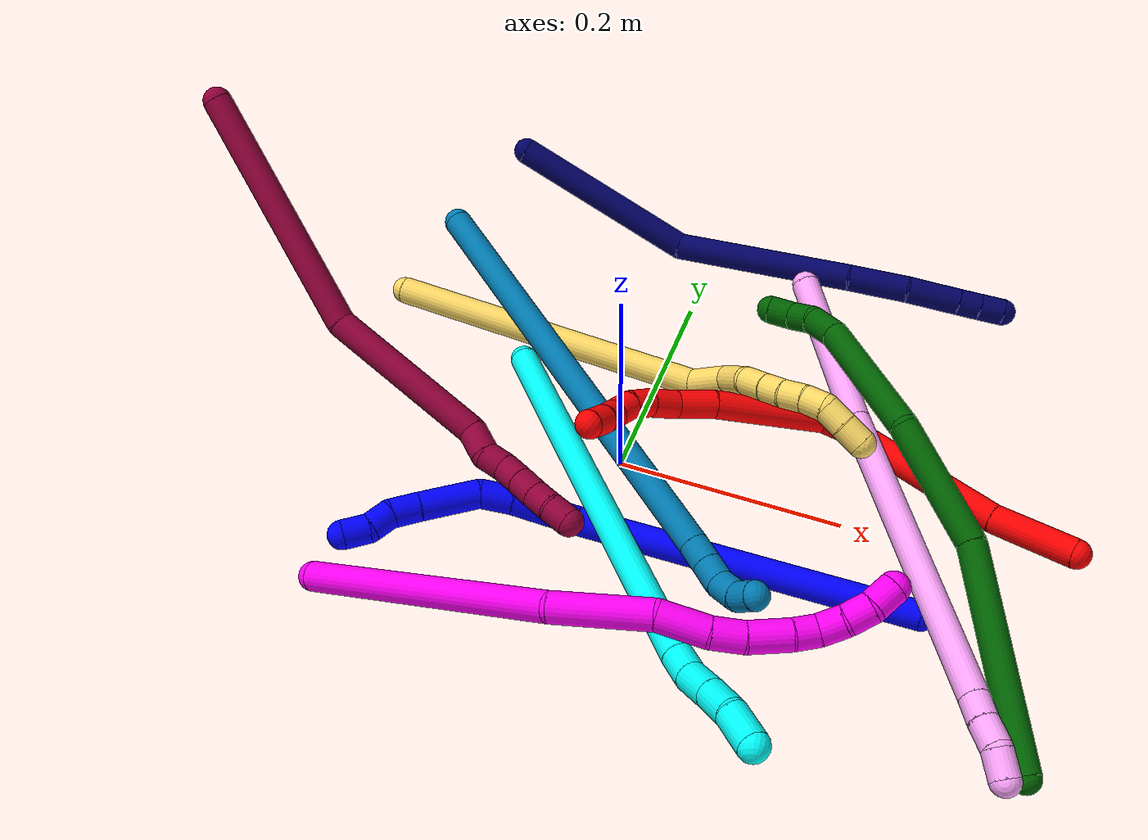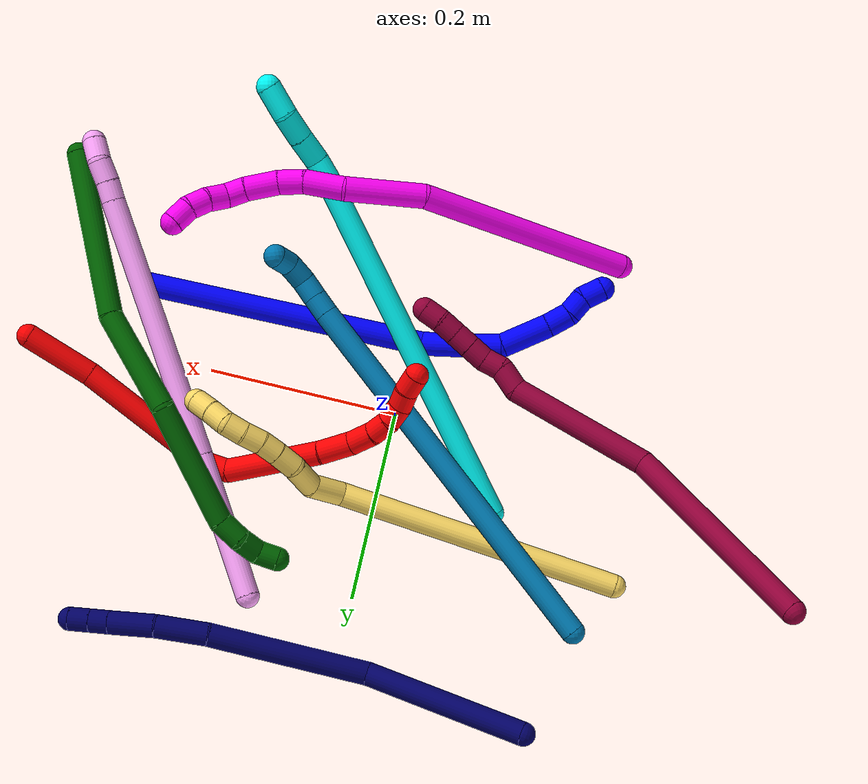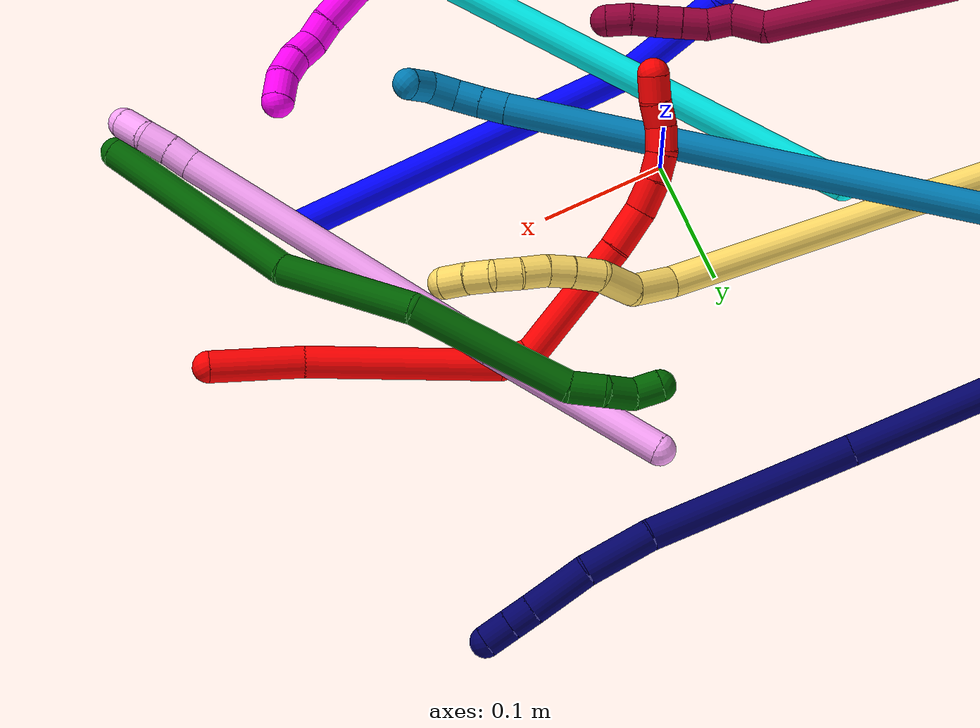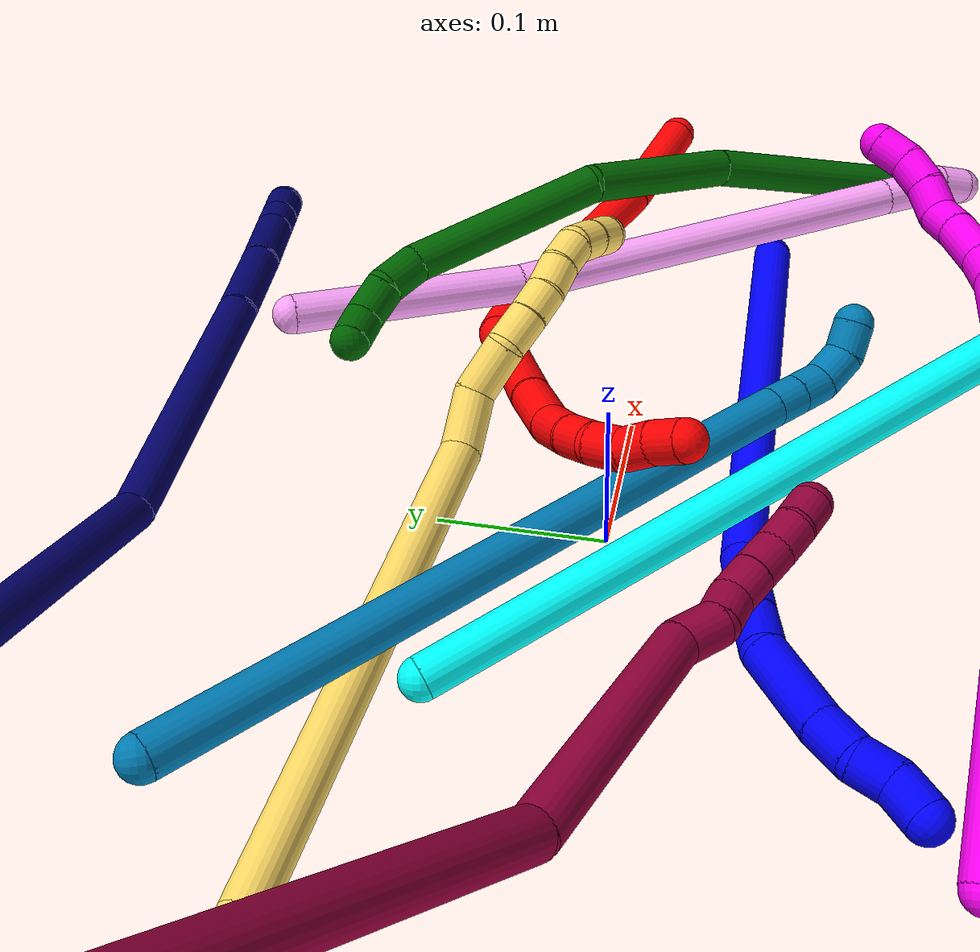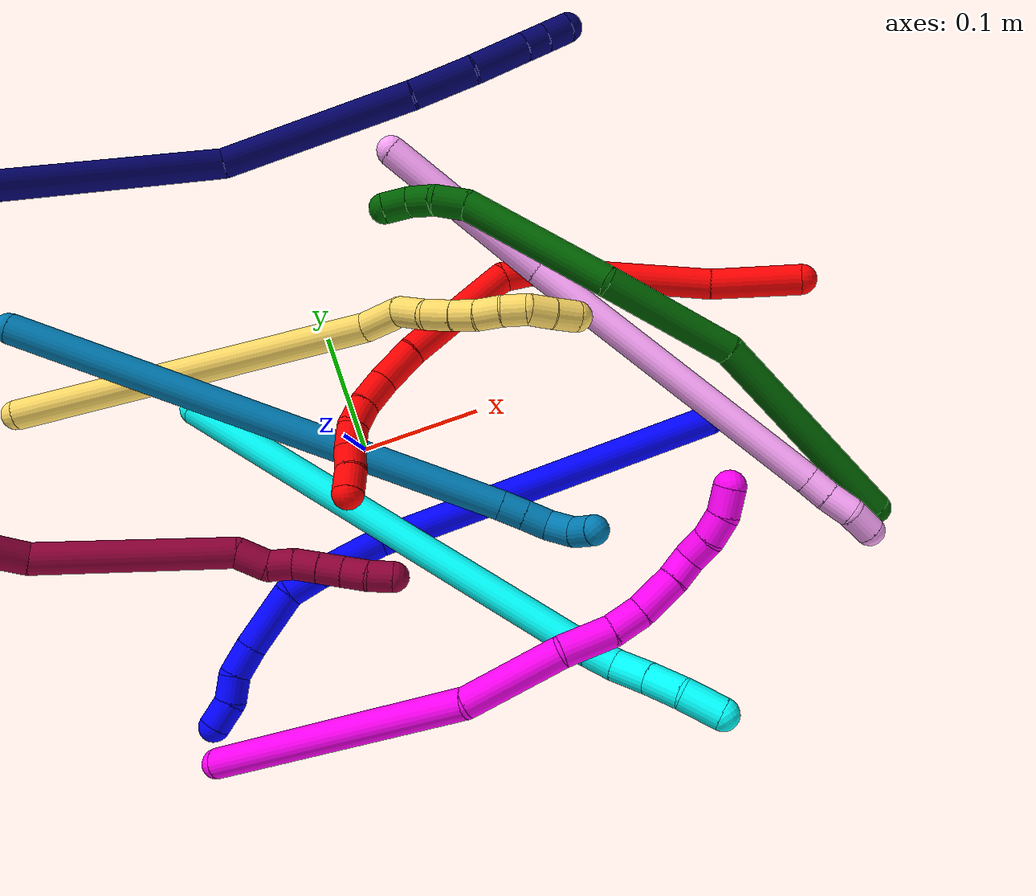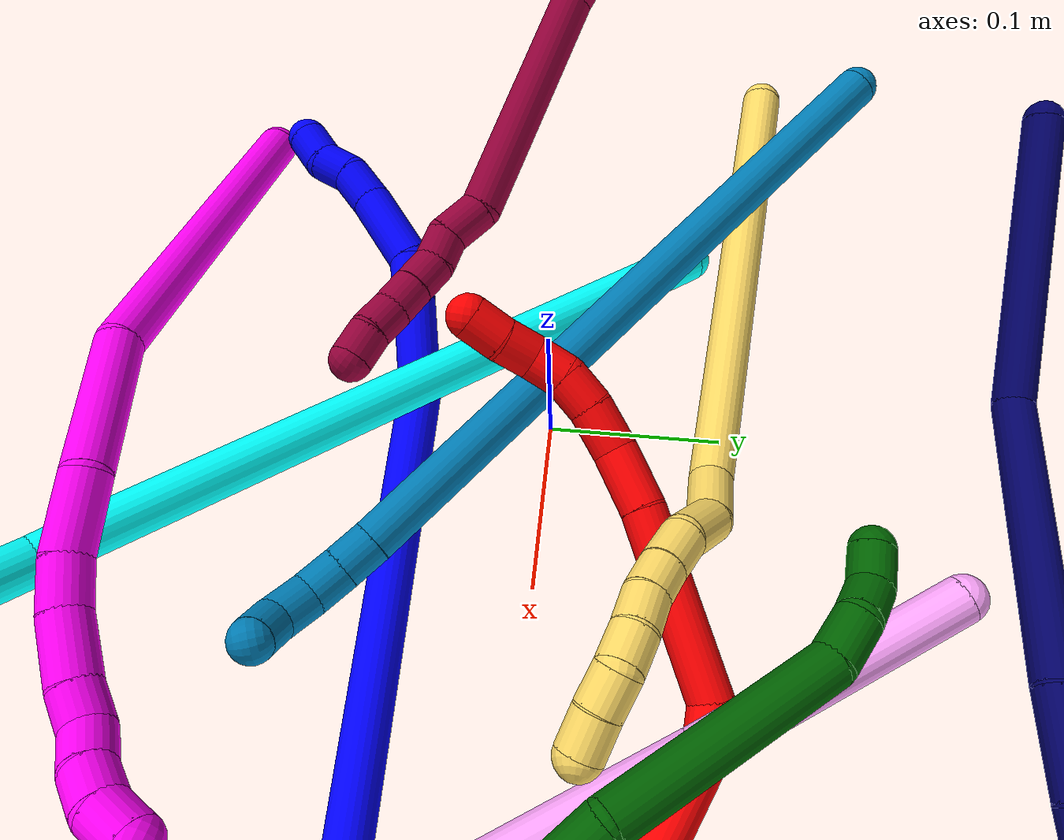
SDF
<sdf version="1.7">
 <world name="default">
  <plugin name="TubeGeneratorPlugin" filename="libtube_generator_plugin.so"/>
  <model name="photoneo_s_sensor">
   <static>1</static>
   <pose>0 0 2 1.57079 1.57079 3.14159</pose>
   <link name="link">
    <inertial><mass>0.1</mass></inertial>
    <sensor name="sensor" type="depth">
     <update_rate>30</update_rate>
     <camera>
      <horizontal_fov>1.22</horizontal_fov>
      <image><width>1920</width><height>1200</height><format>B8G8R8</format></image>
      <clip><near>0.1</near><far>2</far></clip>
      <depth_camera><output>points</output></depth_camera>
     </camera>
     <plugin name="camera_plugin" filename="libgazebo_ros_depth_camera.so">
      <baseline>0.2</baseline>
      <alwaysOn>1</alwaysOn>
      <updateRate>0.0</updateRate>
      <cameraName>camera_ir</cameraName>
      <imageTopicName>/camera/color/image_raw</imageTopicName>
      <cameraInfoTopicName>/camera/color/camera_info</cameraInfoTopicName>
      <depthImageTopicName>/camera/depth/image_raw</depthImageTopicName>
      <depthImageCameraInfoTopicName>/camera/depth/camera_info</depthImageCameraInfoTopicName>
      <pointCloudTopicName>/camera/depth/points</pointCloudTopicName>
      <frameName>fr_optical</frameName>
      <pointCloudCutoff>0.1</pointCloudCutoff>
      <pointCloudCutoffMax>2.0</pointCloudCutoffMax>
      <distortionK1>0</distortionK1>
      <distortionK2>0</distortionK2>
      <distortionK3>0</distortionK3>
      <distortionT1>0</distortionT1>
      <distortionT2>0</distortionT2>
      <CxPrime>0</CxPrime>
      <Cx>0</Cx>
      <Cy>0</Cy>
      <focalLength>0</focalLength>
      <hackBaseline>0</hackBaseline>
     </plugin>
    </sensor>
   </link>
  </model>
  <gravity>0 0 -9.8</gravity>
  <magnetic_field>6e-06 2.3e-05 -4.2e-05</magnetic_field>
  <atmosphere type="adiabatic"/>
  <physics name="default_physics" default="0" type="ode">
   <max_step_size>0.003</max_step_size>
   <real_time_factor>1</real_time_factor>
   <real_time_update_rate>1000</real_time_update_rate>
   <max_contacts>10000</max_contacts>
   <ode>
    <solver>
     <type>quick</type>
     <iters>100</iters>
     <sor>1.3</sor>
     <use_dynamic_moi_rescaling>0</use_dynamic_moi_rescaling>
    </solver>
    <constraints>
     <contact_max_correcting_vel>0</contact_max_correcting_vel>
     <contact_surface_layer>0.001</contact_surface_layer>
     <cfm>0</cfm>
     <erp>0.2</erp>
    </constraints>
   </ode>
  </physics>
  <scene><ambient>0.4 0.4 0.4 1</ambient><background>0.7 0.7 0.7 1</background><shadows>0</shadows></scene>
  <audio><device>default</device></audio>
  <spherical_coordinates>
   <surface_model>EARTH_WGS84</surface_model>
   <latitude_deg>0</latitude_deg>
   <longitude_deg>0</longitude_deg>
   <elevation>0</elevation>
   <heading_deg>0</heading_deg>
  </spherical_coordinates>
  <model name="bin">
   <static>1</static>
   <link name="bottom">
    <collision name="collision-bottom">
     <pose>0 0 -0.01 0 -0 0</pose>
     <geometry><box><size>0.8 0.6 0.02</size></box></geometry>
     <surface>
      <friction><ode><mu>100</mu><mu2>100</mu2></ode></friction>
      <contact><collide_bitmask>65535</collide_bitmask></contact>
     </surface>
    </collision>
   </link>
   <link name="west_wall">
    <collision name="collision-west_wall">
     <pose>-0.41 0 0.1 0 -0 0</pose>
     <geometry><box><size>0.02 0.6 0.2</size></box></geometry>
     <surface>
      <friction><ode><mu>100</mu><mu2>100</mu2></ode></friction>
      <contact><collide_bitmask>65535</collide_bitmask></contact>
     </surface>
    </collision>
   </link>
   <link name="east_wall">
    <collision name="collision-east_wall">
     <pose>0.41 0 0.1 0 -0 0</pose>
     <geometry><box><size>0.02 0.6 0.2</size></box></geometry>
     <surface>
      <friction><ode><mu>100</mu><mu2>100</mu2></ode></friction>
      <contact><collide_bitmask>65535</collide_bitmask></contact>
     </surface>
    </collision>
   </link>
   <link name="south_wall">
    <collision name="collision-south_wall">
     <pose>0 -0.31 0.1 0 -0 0</pose>
     <geometry><box><size>0.8 0.02 0.2</size></box></geometry>
     <surface>
      <friction><ode><mu>100</mu><mu2>100</mu2></ode></friction>
      <contact><collide_bitmask>65535</collide_bitmask></contact>
     </surface>
    </collision>
   </link>
   <link name="north_wall">
    <collision name="collision-north_wall">
     <pose>0 0.31 0.1 0 -0 0</pose>
     <geometry><box><size>0.8 0.02 0.2</size></box></geometry>
     <surface>
      <friction><ode><mu>100</mu><mu2>100</mu2></ode></friction>
      <contact><collide_bitmask>65535</collide_bitmask></contact>
     </surface>
    </collision>
   </link>
  </model>
  <model name="1">
   <static>0</static>
   <link name="1">
    <collision name="collision-cylinder-e_1_1_4">
     <pose>-0.093736 -0.003088 -0.113009 3.11428 -0.692261 -3.06588</pose>
     <geometry><cylinder><radius>0.0125</radius><length>0.293713</length></cylinder></geometry>
     <surface>
      <friction><ode><mu>1.16</mu><mu2>1.16</mu2><slip1>0</slip1><slip2>0</slip2></ode></friction>
      <contact><ode><kp>1e+06</kp><kd>1</kd><max_vel>0</max_vel><min_depth>0.001</min_depth></ode></contact>
     </surface>
    </collision>
    <visual name="visual-cylinder-e_1_1_4">
     <pose>-0.093736 -0.003088 -0.113009 3.11428 -0.692261 -3.06588</pose>
     <geometry><cylinder><radius>0.0125</radius><length>0.293713</length></cylinder></geometry>
     <material><ambient>0 0 1 1</ambient></material>
    </visual>
    <collision name="collision-cylinder-e_2_4_5">
     <pose>-0.211176 -0.001875 -0.241875 -2.87675 -0.964704 2.64337</pose>
     <geometry><cylinder><radius>0.0125</radius><length>0.057684</length></cylinder></geometry>
     <surface>
      <friction><ode><mu>1.16</mu><mu2>1.16</mu2><slip1>0</slip1><slip2>0</slip2></ode></friction>
      <contact><ode><kp>1e+06</kp><kd>1</kd><max_vel>0</max_vel><min_depth>0.001</min_depth></ode></contact>
     </surface>
    </collision>
    <visual name="visual-cylinder-e_2_4_5">
     <pose>-0.211176 -0.001875 -0.241875 -2.87675 -0.964704 2.64337</pose>
     <geometry><cylinder><radius>0.0125</radius><length>0.057684</length></cylinder></geometry>
     <material><ambient>0 0 1 1</ambient></material>
    </visual>
    <collision name="collision-cylinder-e_3_5_6">
     <pose>-0.246309 0.002847 -0.265511 -3.08748 -0.97254 3.03929</pose>
     <geometry><cylinder><radius>0.0125</radius><length>0.027662</length></cylinder></geometry>
     <surface>
      <friction><ode><mu>1.16</mu><mu2>1.16</mu2><slip1>0</slip1><slip2>0</slip2></ode></friction>
      <contact><ode><kp>1e+06</kp><kd>1</kd><max_vel>0</max_vel><min_depth>0.001</min_depth></ode></contact>
     </surface>
    </collision>
    <visual name="visual-cylinder-e_3_5_6">
     <pose>-0.246309 0.002847 -0.265511 -3.08748 -0.97254 3.03929</pose>
     <geometry><cylinder><radius>0.0125</radius><length>0.027662</length></cylinder></geometry>
     <material><ambient>0 0 1 1</ambient></material>
    </visual>
    <collision name="collision-cylinder-e_4_6_7">
     <pose>-0.281293 -0.004279 -0.280848 2.35694 -1.14503 -2.00014</pose>
     <geometry><cylinder><radius>0.0125</radius><length>0.051726</length></cylinder></geometry>
     <surface>
      <friction><ode><mu>1.16</mu><mu2>1.16</mu2><slip1>0</slip1><slip2>0</slip2></ode></friction>
      <contact><ode><kp>1e+06</kp><kd>1</kd><max_vel>0</max_vel><min_depth>0.001</min_depth></ode></contact>
     </surface>
    </collision>
    <visual name="visual-cylinder-e_4_6_7">
     <pose>-0.281293 -0.004279 -0.280848 2.35694 -1.14503 -2.00014</pose>
     <geometry><cylinder><radius>0.0125</radius><length>0.051726</length></cylinder></geometry>
     <material><ambient>0 0 1 1</ambient></material>
    </visual>
    <collision name="collision-cylinder-e_5_7_8">
     <pose>-0.316843 -0.014987 -0.29062 2.18174 -1.25968 -1.90128</pose>
     <geometry><cylinder><radius>0.0125</radius><length>0.025202</length></cylinder></geometry>
     <surface>
      <friction><ode><mu>1.16</mu><mu2>1.16</mu2><slip1>0</slip1><slip2>0</slip2></ode></friction>
      <contact><ode><kp>1e+06</kp><kd>1</kd><max_vel>0</max_vel><min_depth>0.001</min_depth></ode></contact>
     </surface>
    </collision>
    <visual name="visual-cylinder-e_5_7_8">
     <pose>-0.316843 -0.014987 -0.29062 2.18174 -1.25968 -1.90128</pose>
     <geometry><cylinder><radius>0.0125</radius><length>0.025202</length></cylinder></geometry>
     <material><ambient>0 0 1 1</ambient></material>
    </visual>
    <collision name="collision-cylinder-e_6_8_9">
     <pose>-0.338213 -0.023264 -0.291563 1.3276 -1.05846 -0.858152</pose>
     <geometry><cylinder><radius>0.0125</radius><length>0.021511</length></cylinder></geometry>
     <surface>
      <friction><ode><mu>1.16</mu><mu2>1.16</mu2><slip1>0</slip1><slip2>0</slip2></ode></friction>
      <contact><ode><kp>1e+06</kp><kd>1</kd><max_vel>0</max_vel><min_depth>0.001</min_depth></ode></contact>
     </surface>
    </collision>
    <visual name="visual-cylinder-e_6_8_9">
     <pose>-0.338213 -0.023264 -0.291563 1.3276 -1.05846 -0.858152</pose>
     <geometry><cylinder><radius>0.0125</radius><length>0.021511</length></cylinder></geometry>
     <material><ambient>0 0 1 1</ambient></material>
    </visual>
    <collision name="collision-cylinder-e_7_9_2">
     <pose>-0.357963 -0.03167 -0.293141 2.28436 -1.17377 -1.93758</pose>
     <geometry><cylinder><radius>0.0125</radius><length>0.022501</length></cylinder></geometry>
     <surface>
      <friction><ode><mu>1.16</mu><mu2>1.16</mu2><slip1>0</slip1><slip2>0</slip2></ode></friction>
      <contact><ode><kp>1e+06</kp><kd>1</kd><max_vel>0</max_vel><min_depth>0.001</min_depth></ode></contact>
     </surface>
    </collision>
    <visual name="visual-cylinder-e_7_9_2">
     <pose>-0.357963 -0.03167 -0.293141 2.28436 -1.17377 -1.93758</pose>
     <geometry><cylinder><radius>0.0125</radius><length>0.022501</length></cylinder></geometry>
     <material><ambient>0 0 1 1</ambient></material>
    </visual>
    <collision name="collision-sphere-2">
     <pose>-0.368339 -0.034959 -0.295988 0 -0 0</pose>
     <geometry><sphere><radius>0.0125</radius></sphere></geometry>
     <surface>
      <friction><ode><mu>1.16</mu><mu2>1.16</mu2><slip1>0</slip1><slip2>0</slip2></ode></friction>
      <contact><ode><kp>1e+06</kp><kd>1</kd><max_vel>0</max_vel><min_depth>0.001</min_depth></ode></contact>
     </surface>
    </collision>
    <visual name="visual-sphere-2">
     <pose>-0.368339 -0.034959 -0.295988 0 -0 0</pose>
     <geometry><sphere><radius>0.0125</radius></sphere></geometry>
     <material><ambient>0 0 1 1</ambient></material>
    </visual>
    <collision name="collision-sphere-9">
     <pose>-0.347587 -0.028381 -0.290293 0 -0 0</pose>
     <geometry><sphere><radius>0.0125</radius></sphere></geometry>
     <surface>
      <friction><ode><mu>1.16</mu><mu2>1.16</mu2><slip1>0</slip1><slip2>0</slip2></ode></friction>
      <contact><ode><kp>1e+06</kp><kd>1</kd><max_vel>0</max_vel><min_depth>0.001</min_depth></ode></contact>
     </surface>
    </collision>
    <visual name="visual-sphere-9">
     <pose>-0.347587 -0.028381 -0.290293 0 -0 0</pose>
     <geometry><sphere><radius>0.0125</radius></sphere></geometry>
     <material><ambient>0 0 1 1</ambient></material>
    </visual>
    <collision name="collision-sphere-4">
     <pose>-0.187471 -0.006176 -0.226018 0 -0 0</pose>
     <geometry><sphere><radius>0.0125</radius></sphere></geometry>
     <surface>
      <friction><ode><mu>1.16</mu><mu2>1.16</mu2><slip1>0</slip1><slip2>0</slip2></ode></friction>
      <contact><ode><kp>1e+06</kp><kd>1</kd><max_vel>0</max_vel><min_depth>0.001</min_depth></ode></contact>
     </surface>
    </collision>
    <visual name="visual-sphere-4">
     <pose>-0.187471 -0.006176 -0.226018 0 -0 0</pose>
     <geometry><sphere><radius>0.0125</radius></sphere></geometry>
     <material><ambient>0 0 1 1</ambient></material>
    </visual>
    <collision name="collision-sphere-1">
     <geometry><sphere><radius>0.0125</radius></sphere></geometry>
     <surface>
      <friction><ode><mu>1.16</mu><mu2>1.16</mu2><slip1>0</slip1><slip2>0</slip2></ode></friction>
      <contact><ode><kp>1e+06</kp><kd>1</kd><max_vel>0</max_vel><min_depth>0.001</min_depth></ode></contact>
     </surface>
    </collision>
    <visual name="visual-sphere-1">
     <geometry><sphere><radius>0.0125</radius></sphere></geometry>
     <material><ambient>0 0 1 1</ambient></material>
    </visual>
    <collision name="collision-sphere-8">
     <pose>-0.328839 -0.018146 -0.292832 0 -0 0</pose>
     <geometry><sphere><radius>0.0125</radius></sphere></geometry>
     <surface>
      <friction><ode><mu>1.16</mu><mu2>1.16</mu2><slip1>0</slip1><slip2>0</slip2></ode></friction>
      <contact><ode><kp>1e+06</kp><kd>1</kd><max_vel>0</max_vel><min_depth>0.001</min_depth></ode></contact>
     </surface>
    </collision>
    <visual name="visual-sphere-8">
     <pose>-0.328839 -0.018146 -0.292832 0 -0 0</pose>
     <geometry><sphere><radius>0.0125</radius></sphere></geometry>
     <material><ambient>0 0 1 1</ambient></material>
    </visual>
    <collision name="collision-sphere-5">
     <pose>-0.23488 0.002426 -0.257732 0 -0 0</pose>
     <geometry><sphere><radius>0.0125</radius></sphere></geometry>
     <surface>
      <friction><ode><mu>1.16</mu><mu2>1.16</mu2><slip1>0</slip1><slip2>0</slip2></ode></friction>
      <contact><ode><kp>1e+06</kp><kd>1</kd><max_vel>0</max_vel><min_depth>0.001</min_depth></ode></contact>
     </surface>
    </collision>
    <visual name="visual-sphere-5">
     <pose>-0.23488 0.002426 -0.257732 0 -0 0</pose>
     <geometry><sphere><radius>0.0125</radius></sphere></geometry>
     <material><ambient>0 0 1 1</ambient></material>
    </visual>
    <collision name="collision-sphere-6">
     <pose>-0.257738 0.003268 -0.273289 0 -0 0</pose>
     <geometry><sphere><radius>0.0125</radius></sphere></geometry>
     <surface>
      <friction><ode><mu>1.16</mu><mu2>1.16</mu2><slip1>0</slip1><slip2>0</slip2></ode></friction>
      <contact><ode><kp>1e+06</kp><kd>1</kd><max_vel>0</max_vel><min_depth>0.001</min_depth></ode></contact>
     </surface>
    </collision>
    <visual name="visual-sphere-6">
     <pose>-0.257738 0.003268 -0.273289 0 -0 0</pose>
     <geometry><sphere><radius>0.0125</radius></sphere></geometry>
     <material><ambient>0 0 1 1</ambient></material>
    </visual>
    <collision name="collision-sphere-7">
     <pose>-0.304847 -0.011827 -0.288407 0 -0 0</pose>
     <geometry><sphere><radius>0.0125</radius></sphere></geometry>
     <surface>
      <friction><ode><mu>1.16</mu><mu2>1.16</mu2><slip1>0</slip1><slip2>0</slip2></ode></friction>
      <contact><ode><kp>1e+06</kp><kd>1</kd><max_vel>0</max_vel><min_depth>0.001</min_depth></ode></contact>
     </surface>
    </collision>
    <visual name="visual-sphere-7">
     <pose>-0.304847 -0.011827 -0.288407 0 -0 0</pose>
     <geometry><sphere><radius>0.0125</radius></sphere></geometry>
     <material><ambient>0 0 1 1</ambient></material>
    </visual>
    <inertial>
     <pose>-0.168783 -0.005497 -0.178417 0 -0 0</pose>
     <mass>0.5</mass>
     <inertia>
      <ixx>-0.001797</ixx>
      <ixy>0</ixy>
      <ixz>0</ixz>
      <iyy>0.002028</iyy>
      <iyz>0</iyz>
      <izz>0.001415</izz>
     </inertia>
    </inertial>
   </link>
   <pose>0.283133 -0.073334 0.011512 1.22012 0.418722 0.816906</pose>
  </model>
  <model name="2">
   <static>0</static>
   <link name="2">
    <collision name="collision-cylinder-e_1_1_4">
     <pose>-0.001713 -0.025218 -0.027058 2.39136 -0.046279 -0.117416</pose>
     <geometry><cylinder><radius>0.0125</radius><length>0.074054</length></cylinder></geometry>
     <surface>
      <friction><ode><mu>1.16</mu><mu2>1.16</mu2><slip1>0</slip1><slip2>0</slip2></ode></friction>
      <contact><ode><kp>1e+06</kp><kd>1</kd><max_vel>0</max_vel><min_depth>0.001</min_depth></ode></contact>
     </surface>
    </collision>
    <visual name="visual-cylinder-e_1_1_4">
     <pose>-0.001713 -0.025218 -0.027058 2.39136 -0.046279 -0.117416</pose>
     <geometry><cylinder><radius>0.0125</radius><length>0.074054</length></cylinder></geometry>
     <material><ambient>1 0 0 1</ambient></material>
    </visual>
    <collision name="collision-cylinder-e_2_4_5">
     <pose>0.002891 -0.097958 -0.113274 2.46485 0.083058 0.235072</pose>
     <geometry><cylinder><radius>0.0125</radius><length>0.152289</length></cylinder></geometry>
     <surface>
      <friction><ode><mu>1.16</mu><mu2>1.16</mu2><slip1>0</slip1><slip2>0</slip2></ode></friction>
      <contact><ode><kp>1e+06</kp><kd>1</kd><max_vel>0</max_vel><min_depth>0.001</min_depth></ode></contact>
     </surface>
    </collision>
    <visual name="visual-cylinder-e_2_4_5">
     <pose>0.002891 -0.097958 -0.113274 2.46485 0.083058 0.235072</pose>
     <geometry><cylinder><radius>0.0125</radius><length>0.152289</length></cylinder></geometry>
     <material><ambient>1 0 0 1</ambient></material>
    </visual>
    <collision name="collision-cylinder-e_3_5_6">
     <pose>0.007115 -0.149519 -0.183977 2.805 -0.169557 -0.927579</pose>
     <geometry><cylinder><radius>0.0125</radius><length>0.024816</length></cylinder></geometry>
     <surface>
      <friction><ode><mu>1.16</mu><mu2>1.16</mu2><slip1>0</slip1><slip2>0</slip2></ode></friction>
      <contact><ode><kp>1e+06</kp><kd>1</kd><max_vel>0</max_vel><min_depth>0.001</min_depth></ode></contact>
     </surface>
    </collision>
    <visual name="visual-cylinder-e_3_5_6">
     <pose>0.007115 -0.149519 -0.183977 2.805 -0.169557 -0.927579</pose>
     <geometry><cylinder><radius>0.0125</radius><length>0.024816</length></cylinder></geometry>
     <material><ambient>1 0 0 1</ambient></material>
    </visual>
    <collision name="collision-cylinder-e_4_6_7">
     <pose>-0.022349 -0.152012 -0.23982 -3.10671 -0.553157 3.01886</pose>
     <geometry><cylinder><radius>0.0125</radius><length>0.10419</length></cylinder></geometry>
     <surface>
      <friction><ode><mu>1.16</mu><mu2>1.16</mu2><slip1>0</slip1><slip2>0</slip2></ode></friction>
      <contact><ode><kp>1e+06</kp><kd>1</kd><max_vel>0</max_vel><min_depth>0.001</min_depth></ode></contact>
     </surface>
    </collision>
    <visual name="visual-cylinder-e_4_6_7">
     <pose>-0.022349 -0.152012 -0.23982 -3.10671 -0.553157 3.01886</pose>
     <geometry><cylinder><radius>0.0125</radius><length>0.10419</length></cylinder></geometry>
     <material><ambient>1 0 0 1</ambient></material>
    </visual>
    <collision name="collision-cylinder-e_5_7_8">
     <pose>-0.060815 -0.150325 -0.297715 -3.13121 -0.684482 3.11245</pose>
     <geometry><cylinder><radius>0.0125</radius><length>0.035101</length></cylinder></geometry>
     <surface>
      <friction><ode><mu>1.16</mu><mu2>1.16</mu2><slip1>0</slip1><slip2>0</slip2></ode></friction>
      <contact><ode><kp>1e+06</kp><kd>1</kd><max_vel>0</max_vel><min_depth>0.001</min_depth></ode></contact>
     </surface>
    </collision>
    <visual name="visual-cylinder-e_5_7_8">
     <pose>-0.060815 -0.150325 -0.297715 -3.13121 -0.684482 3.11245</pose>
     <geometry><cylinder><radius>0.0125</radius><length>0.035101</length></cylinder></geometry>
     <material><ambient>1 0 0 1</ambient></material>
    </visual>
    <collision name="collision-cylinder-e_6_8_9">
     <pose>-0.079738 -0.14646 -0.321669 -2.79638 -0.618115 2.14201</pose>
     <geometry><cylinder><radius>0.0125</radius><length>0.02701</length></cylinder></geometry>
     <surface>
      <friction><ode><mu>1.16</mu><mu2>1.16</mu2><slip1>0</slip1><slip2>0</slip2></ode></friction>
      <contact><ode><kp>1e+06</kp><kd>1</kd><max_vel>0</max_vel><min_depth>0.001</min_depth></ode></contact>
     </surface>
    </collision>
    <visual name="visual-cylinder-e_6_8_9">
     <pose>-0.079738 -0.14646 -0.321669 -2.79638 -0.618115 2.14201</pose>
     <geometry><cylinder><radius>0.0125</radius><length>0.02701</length></cylinder></geometry>
     <material><ambient>1 0 0 1</ambient></material>
    </visual>
    <collision name="collision-cylinder-e_7_9_10">
     <pose>-0.094698 -0.13892 -0.33876 -2.62611 -0.744712 1.95421</pose>
     <geometry><cylinder><radius>0.0125</radius><length>0.021053</length></cylinder></geometry>
     <surface>
      <friction><ode><mu>1.16</mu><mu2>1.16</mu2><slip1>0</slip1><slip2>0</slip2></ode></friction>
      <contact><ode><kp>1e+06</kp><kd>1</kd><max_vel>0</max_vel><min_depth>0.001</min_depth></ode></contact>
     </surface>
    </collision>
    <visual name="visual-cylinder-e_7_9_10">
     <pose>-0.094698 -0.13892 -0.33876 -2.62611 -0.744712 1.95421</pose>
     <geometry><cylinder><radius>0.0125</radius><length>0.021053</length></cylinder></geometry>
     <material><ambient>1 0 0 1</ambient></material>
    </visual>
    <collision name="collision-cylinder-e_8_10_11">
     <pose>-0.110325 -0.130772 -0.349237 -2.28331 -0.977613 1.72065</pose>
     <geometry><cylinder><radius>0.0125</radius><length>0.020483</length></cylinder></geometry>
     <surface>
      <friction><ode><mu>1.16</mu><mu2>1.16</mu2><slip1>0</slip1><slip2>0</slip2></ode></friction>
      <contact><ode><kp>1e+06</kp><kd>1</kd><max_vel>0</max_vel><min_depth>0.001</min_depth></ode></contact>
     </surface>
    </collision>
    <visual name="visual-cylinder-e_8_10_11">
     <pose>-0.110325 -0.130772 -0.349237 -2.28331 -0.977613 1.72065</pose>
     <geometry><cylinder><radius>0.0125</radius><length>0.020483</length></cylinder></geometry>
     <material><ambient>1 0 0 1</ambient></material>
    </visual>
    <collision name="collision-cylinder-e_9_11_12">
     <pose>-0.125112 -0.119125 -0.356076 -1.97125 -0.670197 0.967783</pose>
     <geometry><cylinder><radius>0.0125</radius><length>0.02027</length></cylinder></geometry>
     <surface>
      <friction><ode><mu>1.16</mu><mu2>1.16</mu2><slip1>0</slip1><slip2>0</slip2></ode></friction>
      <contact><ode><kp>1e+06</kp><kd>1</kd><max_vel>0</max_vel><min_depth>0.001</min_depth></ode></contact>
     </surface>
    </collision>
    <visual name="visual-cylinder-e_9_11_12">
     <pose>-0.125112 -0.119125 -0.356076 -1.97125 -0.670197 0.967783</pose>
     <geometry><cylinder><radius>0.0125</radius><length>0.02027</length></cylinder></geometry>
     <material><ambient>1 0 0 1</ambient></material>
    </visual>
    <collision name="collision-cylinder-e_10_12_2">
     <pose>-0.138441 -0.105514 -0.363455 -2.16802 -0.745753 1.27297</pose>
     <geometry><cylinder><radius>0.0125</radius><length>0.020734</length></cylinder></geometry>
     <surface>
      <friction><ode><mu>1.16</mu><mu2>1.16</mu2><slip1>0</slip1><slip2>0</slip2></ode></friction>
      <contact><ode><kp>1e+06</kp><kd>1</kd><max_vel>0</max_vel><min_depth>0.001</min_depth></ode></contact>
     </surface>
    </collision>
    <visual name="visual-cylinder-e_10_12_2">
     <pose>-0.138441 -0.105514 -0.363455 -2.16802 -0.745753 1.27297</pose>
     <geometry><cylinder><radius>0.0125</radius><length>0.020734</length></cylinder></geometry>
     <material><ambient>1 0 0 1</ambient></material>
    </visual>
    <collision name="collision-sphere-2">
     <pose>-0.145475 -0.099217 -0.367737 0 -0 0</pose>
     <geometry><sphere><radius>0.0125</radius></sphere></geometry>
     <surface>
      <friction><ode><mu>1.16</mu><mu2>1.16</mu2><slip1>0</slip1><slip2>0</slip2></ode></friction>
      <contact><ode><kp>1e+06</kp><kd>1</kd><max_vel>0</max_vel><min_depth>0.001</min_depth></ode></contact>
     </surface>
    </collision>
    <visual name="visual-sphere-2">
     <pose>-0.145475 -0.099217 -0.367737 0 -0 0</pose>
     <geometry><sphere><radius>0.0125</radius></sphere></geometry>
     <material><ambient>1 0 0 1</ambient></material>
    </visual>
    <collision name="collision-sphere-12">
     <pose>-0.131407 -0.111811 -0.359172 0 -0 0</pose>
     <geometry><sphere><radius>0.0125</radius></sphere></geometry>
     <surface>
      <friction><ode><mu>1.16</mu><mu2>1.16</mu2><slip1>0</slip1><slip2>0</slip2></ode></friction>
      <contact><ode><kp>1e+06</kp><kd>1</kd><max_vel>0</max_vel><min_depth>0.001</min_depth></ode></contact>
     </surface>
    </collision>
    <visual name="visual-sphere-12">
     <pose>-0.131407 -0.111811 -0.359172 0 -0 0</pose>
     <geometry><sphere><radius>0.0125</radius></sphere></geometry>
     <material><ambient>1 0 0 1</ambient></material>
    </visual>
    <collision name="collision-sphere-11">
     <pose>-0.118817 -0.12644 -0.352979 0 -0 0</pose>
     <geometry><sphere><radius>0.0125</radius></sphere></geometry>
     <surface>
      <friction><ode><mu>1.16</mu><mu2>1.16</mu2><slip1>0</slip1><slip2>0</slip2></ode></friction>
      <contact><ode><kp>1e+06</kp><kd>1</kd><max_vel>0</max_vel><min_depth>0.001</min_depth></ode></contact>
     </surface>
    </collision>
    <visual name="visual-sphere-11">
     <pose>-0.118817 -0.12644 -0.352979 0 -0 0</pose>
     <geometry><sphere><radius>0.0125</radius></sphere></geometry>
     <material><ambient>1 0 0 1</ambient></material>
    </visual>
    <collision name="collision-sphere-10">
     <pose>-0.101833 -0.135104 -0.345494 0 -0 0</pose>
     <geometry><sphere><radius>0.0125</radius></sphere></geometry>
     <surface>
      <friction><ode><mu>1.16</mu><mu2>1.16</mu2><slip1>0</slip1><slip2>0</slip2></ode></friction>
      <contact><ode><kp>1e+06</kp><kd>1</kd><max_vel>0</max_vel><min_depth>0.001</min_depth></ode></contact>
     </surface>
    </collision>
    <visual name="visual-sphere-10">
     <pose>-0.101833 -0.135104 -0.345494 0 -0 0</pose>
     <geometry><sphere><radius>0.0125</radius></sphere></geometry>
     <material><ambient>1 0 0 1</ambient></material>
    </visual>
    <collision name="collision-sphere-9">
     <pose>-0.087564 -0.142735 -0.332026 0 -0 0</pose>
     <geometry><sphere><radius>0.0125</radius></sphere></geometry>
     <surface>
      <friction><ode><mu>1.16</mu><mu2>1.16</mu2><slip1>0</slip1><slip2>0</slip2></ode></friction>
      <contact><ode><kp>1e+06</kp><kd>1</kd><max_vel>0</max_vel><min_depth>0.001</min_depth></ode></contact>
     </surface>
    </collision>
    <visual name="visual-sphere-9">
     <pose>-0.087564 -0.142735 -0.332026 0 -0 0</pose>
     <geometry><sphere><radius>0.0125</radius></sphere></geometry>
     <material><ambient>1 0 0 1</ambient></material>
    </visual>
    <collision name="collision-sphere-4">
     <pose>-0.003426 -0.050437 -0.054115 0 -0 0</pose>
     <geometry><sphere><radius>0.0125</radius></sphere></geometry>
     <surface>
      <friction><ode><mu>1.16</mu><mu2>1.16</mu2><slip1>0</slip1><slip2>0</slip2></ode></friction>
      <contact><ode><kp>1e+06</kp><kd>1</kd><max_vel>0</max_vel><min_depth>0.001</min_depth></ode></contact>
     </surface>
    </collision>
    <visual name="visual-sphere-4">
     <pose>-0.003426 -0.050437 -0.054115 0 -0 0</pose>
     <geometry><sphere><radius>0.0125</radius></sphere></geometry>
     <material><ambient>1 0 0 1</ambient></material>
    </visual>
    <collision name="collision-sphere-1">
     <geometry><sphere><radius>0.0125</radius></sphere></geometry>
     <surface>
      <friction><ode><mu>1.16</mu><mu2>1.16</mu2><slip1>0</slip1><slip2>0</slip2></ode></friction>
      <contact><ode><kp>1e+06</kp><kd>1</kd><max_vel>0</max_vel><min_depth>0.001</min_depth></ode></contact>
     </surface>
    </collision>
    <visual name="visual-sphere-1">
     <geometry><sphere><radius>0.0125</radius></sphere></geometry>
     <material><ambient>1 0 0 1</ambient></material>
    </visual>
    <collision name="collision-sphere-8">
     <pose>-0.071912 -0.150184 -0.311312 0 -0 0</pose>
     <geometry><sphere><radius>0.0125</radius></sphere></geometry>
     <surface>
      <friction><ode><mu>1.16</mu><mu2>1.16</mu2><slip1>0</slip1><slip2>0</slip2></ode></friction>
      <contact><ode><kp>1e+06</kp><kd>1</kd><max_vel>0</max_vel><min_depth>0.001</min_depth></ode></contact>
     </surface>
    </collision>
    <visual name="visual-sphere-8">
     <pose>-0.071912 -0.150184 -0.311312 0 -0 0</pose>
     <geometry><sphere><radius>0.0125</radius></sphere></geometry>
     <material><ambient>1 0 0 1</ambient></material>
    </visual>
    <collision name="collision-sphere-5">
     <pose>0.009208 -0.145479 -0.172433 0 -0 0</pose>
     <geometry><sphere><radius>0.0125</radius></sphere></geometry>
     <surface>
      <friction><ode><mu>1.16</mu><mu2>1.16</mu2><slip1>0</slip1><slip2>0</slip2></ode></friction>
      <contact><ode><kp>1e+06</kp><kd>1</kd><max_vel>0</max_vel><min_depth>0.001</min_depth></ode></contact>
     </surface>
    </collision>
    <visual name="visual-sphere-5">
     <pose>0.009208 -0.145479 -0.172433 0 -0 0</pose>
     <geometry><sphere><radius>0.0125</radius></sphere></geometry>
     <material><ambient>1 0 0 1</ambient></material>
    </visual>
    <collision name="collision-sphere-6">
     <pose>0.005021 -0.153558 -0.195521 0 -0 0</pose>
     <geometry><sphere><radius>0.0125</radius></sphere></geometry>
     <surface>
      <friction><ode><mu>1.16</mu><mu2>1.16</mu2><slip1>0</slip1><slip2>0</slip2></ode></friction>
      <contact><ode><kp>1e+06</kp><kd>1</kd><max_vel>0</max_vel><min_depth>0.001</min_depth></ode></contact>
     </surface>
    </collision>
    <visual name="visual-sphere-6">
     <pose>0.005021 -0.153558 -0.195521 0 -0 0</pose>
     <geometry><sphere><radius>0.0125</radius></sphere></geometry>
     <material><ambient>1 0 0 1</ambient></material>
    </visual>
    <collision name="collision-sphere-7">
     <pose>-0.049718 -0.150467 -0.284119 0 -0 0</pose>
     <geometry><sphere><radius>0.0125</radius></sphere></geometry>
     <surface>
      <friction><ode><mu>1.16</mu><mu2>1.16</mu2><slip1>0</slip1><slip2>0</slip2></ode></friction>
      <contact><ode><kp>1e+06</kp><kd>1</kd><max_vel>0</max_vel><min_depth>0.001</min_depth></ode></contact>
     </surface>
    </collision>
    <visual name="visual-sphere-7">
     <pose>-0.049718 -0.150467 -0.284119 0 -0 0</pose>
     <geometry><sphere><radius>0.0125</radius></sphere></geometry>
     <material><ambient>1 0 0 1</ambient></material>
    </visual>
    <inertial>
     <pose>-0.031574 -0.111544 -0.193967 0 -0 0</pose>
     <mass>0.5</mass>
     <inertia>
      <ixx>0.00031</ixx>
      <ixy>0</ixy>
      <ixz>0</ixz>
      <iyy>-7.2e-05</iyy>
      <iyz>0</iyz>
      <izz>0.000215</izz>
     </inertia>
    </inertial>
   </link>
   <pose>0.3885 0.008828 0.039139 2.13095 -0.327764 1.2551</pose>
  </model>
  <model name="3">
   <static>0</static>
   <link name="3">
    <collision name="collision-cylinder-e_1_1_4">
     <pose>0.038947 -0.082717 0.170787 0.451029 0.20243 0.046592</pose>
     <geometry><cylinder><radius>0.0125</radius><length>0.387439</length></cylinder></geometry>
     <surface>
      <friction><ode><mu>1.16</mu><mu2>1.16</mu2><slip1>0</slip1><slip2>0</slip2></ode></friction>
      <contact><ode><kp>1e+06</kp><kd>1</kd><max_vel>0</max_vel><min_depth>0.001</min_depth></ode></contact>
     </surface>
    </collision>
    <visual name="visual-cylinder-e_1_1_4">
     <pose>0.038947 -0.082717 0.170787 0.451029 0.20243 0.046592</pose>
     <geometry><cylinder><radius>0.0125</radius><length>0.387439</length></cylinder></geometry>
     <material><ambient>0.003922 1 0.996078 1</ambient></material>
    </visual>
    <collision name="collision-cylinder-e_2_4_5">
     <pose>0.08068 -0.170915 0.351093 0.522494 0.24832 0.066709</pose>
     <geometry><cylinder><radius>0.0125</radius><length>0.022664</length></cylinder></geometry>
     <surface>
      <friction><ode><mu>1.16</mu><mu2>1.16</mu2><slip1>0</slip1><slip2>0</slip2></ode></friction>
      <contact><ode><kp>1e+06</kp><kd>1</kd><max_vel>0</max_vel><min_depth>0.001</min_depth></ode></contact>
     </surface>
    </collision>
    <visual name="visual-cylinder-e_2_4_5">
     <pose>0.08068 -0.170915 0.351093 0.522494 0.24832 0.066709</pose>
     <geometry><cylinder><radius>0.0125</radius><length>0.022664</length></cylinder></geometry>
     <material><ambient>0.003922 1 0.996078 1</ambient></material>
    </visual>
    <collision name="collision-cylinder-e_3_5_6">
     <pose>0.090576 -0.184009 0.370883 0.637821 0.507613 0.170881</pose>
     <geometry><cylinder><radius>0.0125</radius><length>0.029259</length></cylinder></geometry>
     <surface>
      <friction><ode><mu>1.16</mu><mu2>1.16</mu2><slip1>0</slip1><slip2>0</slip2></ode></friction>
      <contact><ode><kp>1e+06</kp><kd>1</kd><max_vel>0</max_vel><min_depth>0.001</min_depth></ode></contact>
     </surface>
    </collision>
    <visual name="visual-cylinder-e_3_5_6">
     <pose>0.090576 -0.184009 0.370883 0.637821 0.507613 0.170881</pose>
     <geometry><cylinder><radius>0.0125</radius><length>0.029259</length></cylinder></geometry>
     <material><ambient>0.003922 1 0.996078 1</ambient></material>
    </visual>
    <collision name="collision-cylinder-e_4_6_7">
     <pose>0.10463 -0.198641 0.391606 0.591465 0.503944 0.156548</pose>
     <geometry><cylinder><radius>0.0125</radius><length>0.028755</length></cylinder></geometry>
     <surface>
      <friction><ode><mu>1.16</mu><mu2>1.16</mu2><slip1>0</slip1><slip2>0</slip2></ode></friction>
      <contact><ode><kp>1e+06</kp><kd>1</kd><max_vel>0</max_vel><min_depth>0.001</min_depth></ode></contact>
     </surface>
    </collision>
    <visual name="visual-cylinder-e_4_6_7">
     <pose>0.10463 -0.198641 0.391606 0.591465 0.503944 0.156548</pose>
     <geometry><cylinder><radius>0.0125</radius><length>0.028755</length></cylinder></geometry>
     <material><ambient>0.003922 1 0.996078 1</ambient></material>
    </visual>
    <collision name="collision-cylinder-e_5_7_2">
     <pose>0.115615 -0.213409 0.415391 0.526357 0.256385 0.06943</pose>
     <geometry><cylinder><radius>0.0125</radius><length>0.031884</length></cylinder></geometry>
     <surface>
      <friction><ode><mu>1.16</mu><mu2>1.16</mu2><slip1>0</slip1><slip2>0</slip2></ode></friction>
      <contact><ode><kp>1e+06</kp><kd>1</kd><max_vel>0</max_vel><min_depth>0.001</min_depth></ode></contact>
     </surface>
    </collision>
    <visual name="visual-cylinder-e_5_7_2">
     <pose>0.115615 -0.213409 0.415391 0.526357 0.256385 0.06943</pose>
     <geometry><cylinder><radius>0.0125</radius><length>0.031884</length></cylinder></geometry>
     <material><ambient>0.003922 1 0.996078 1</ambient></material>
    </visual>
    <collision name="collision-sphere-2">
     <pose>0.119658 -0.221156 0.428724 0 -0 0</pose>
     <geometry><sphere><radius>0.0125</radius></sphere></geometry>
     <surface>
      <friction><ode><mu>1.16</mu><mu2>1.16</mu2><slip1>0</slip1><slip2>0</slip2></ode></friction>
      <contact><ode><kp>1e+06</kp><kd>1</kd><max_vel>0</max_vel><min_depth>0.001</min_depth></ode></contact>
     </surface>
    </collision>
    <visual name="visual-sphere-2">
     <pose>0.119658 -0.221156 0.428724 0 -0 0</pose>
     <geometry><sphere><radius>0.0125</radius></sphere></geometry>
     <material><ambient>0.003922 1 0.996078 1</ambient></material>
    </visual>
    <collision name="collision-sphere-7">
     <pose>0.111573 -0.205662 0.402057 0 -0 0</pose>
     <geometry><sphere><radius>0.0125</radius></sphere></geometry>
     <surface>
      <friction><ode><mu>1.16</mu><mu2>1.16</mu2><slip1>0</slip1><slip2>0</slip2></ode></friction>
      <contact><ode><kp>1e+06</kp><kd>1</kd><max_vel>0</max_vel><min_depth>0.001</min_depth></ode></contact>
     </surface>
    </collision>
    <visual name="visual-sphere-7">
     <pose>0.111573 -0.205662 0.402057 0 -0 0</pose>
     <geometry><sphere><radius>0.0125</radius></sphere></geometry>
     <material><ambient>0.003922 1 0.996078 1</ambient></material>
    </visual>
    <collision name="collision-sphere-6">
     <pose>0.097687 -0.191621 0.381154 0 -0 0</pose>
     <geometry><sphere><radius>0.0125</radius></sphere></geometry>
     <surface>
      <friction><ode><mu>1.16</mu><mu2>1.16</mu2><slip1>0</slip1><slip2>0</slip2></ode></friction>
      <contact><ode><kp>1e+06</kp><kd>1</kd><max_vel>0</max_vel><min_depth>0.001</min_depth></ode></contact>
     </surface>
    </collision>
    <visual name="visual-sphere-6">
     <pose>0.097687 -0.191621 0.381154 0 -0 0</pose>
     <geometry><sphere><radius>0.0125</radius></sphere></geometry>
     <material><ambient>0.003922 1 0.996078 1</ambient></material>
    </visual>
    <collision name="collision-sphere-5">
     <pose>0.083465 -0.176396 0.360612 0 -0 0</pose>
     <geometry><sphere><radius>0.0125</radius></sphere></geometry>
     <surface>
      <friction><ode><mu>1.16</mu><mu2>1.16</mu2><slip1>0</slip1><slip2>0</slip2></ode></friction>
      <contact><ode><kp>1e+06</kp><kd>1</kd><max_vel>0</max_vel><min_depth>0.001</min_depth></ode></contact>
     </surface>
    </collision>
    <visual name="visual-sphere-5">
     <pose>0.083465 -0.176396 0.360612 0 -0 0</pose>
     <geometry><sphere><radius>0.0125</radius></sphere></geometry>
     <material><ambient>0.003922 1 0.996078 1</ambient></material>
    </visual>
    <collision name="collision-sphere-1">
     <geometry><sphere><radius>0.0125</radius></sphere></geometry>
     <surface>
      <friction><ode><mu>1.16</mu><mu2>1.16</mu2><slip1>0</slip1><slip2>0</slip2></ode></friction>
      <contact><ode><kp>1e+06</kp><kd>1</kd><max_vel>0</max_vel><min_depth>0.001</min_depth></ode></contact>
     </surface>
    </collision>
    <visual name="visual-sphere-1">
     <geometry><sphere><radius>0.0125</radius></sphere></geometry>
     <material><ambient>0.003922 1 0.996078 1</ambient></material>
    </visual>
    <collision name="collision-sphere-4">
     <pose>0.077895 -0.165433 0.341575 0 -0 0</pose>
     <geometry><sphere><radius>0.0125</radius></sphere></geometry>
     <surface>
      <friction><ode><mu>1.16</mu><mu2>1.16</mu2><slip1>0</slip1><slip2>0</slip2></ode></friction>
      <contact><ode><kp>1e+06</kp><kd>1</kd><max_vel>0</max_vel><min_depth>0.001</min_depth></ode></contact>
     </surface>
    </collision>
    <visual name="visual-sphere-4">
     <pose>0.077895 -0.165433 0.341575 0 -0 0</pose>
     <geometry><sphere><radius>0.0125</radius></sphere></geometry>
     <material><ambient>0.003922 1 0.996078 1</ambient></material>
    </visual>
    <inertial>
     <pose>0.052526 -0.107642 0.218966 0 -0 0</pose>
     <mass>0.5</mass>
     <inertia>
      <ixx>0.005001</ixx>
      <ixy>0</ixy>
      <ixz>0</ixz>
      <iyy>0.004607</iyy>
      <iyz>0</iyz>
      <izz>0.001133</izz>
     </inertia>
    </inertial>
   </link>
   <pose>-0.122508 0.07688 0.012292 2.08361 -1.54 -0.272068</pose>
  </model>
  <model name="4">
   <static>0</static>
   <link name="4">
    <collision name="collision-cylinder-e_1_1_4">
     <pose>0.013404 -0.070934 -0.025686 1.91822 0.175836 0.250018</pose>
     <geometry><cylinder><radius>0.0125</radius><length>0.153246</length></cylinder></geometry>
     <surface>
      <friction><ode><mu>1.16</mu><mu2>1.16</mu2><slip1>0</slip1><slip2>0</slip2></ode></friction>
      <contact><ode><kp>1e+06</kp><kd>1</kd><max_vel>0</max_vel><min_depth>0.001</min_depth></ode></contact>
     </surface>
    </collision>
    <visual name="visual-cylinder-e_1_1_4">
     <pose>0.013404 -0.070934 -0.025686 1.91822 0.175836 0.250018</pose>
     <geometry><cylinder><radius>0.0125</radius><length>0.153246</length></cylinder></geometry>
     <material><ambient>1 0.65098 0.996078 1</ambient></material>
    </visual>
    <collision name="collision-cylinder-e_2_4_5">
     <pose>0.04358 -0.26639 -0.112298 2.02583 0.120406 0.192594</pose>
     <geometry><cylinder><radius>0.0125</radius><length>0.279277</length></cylinder></geometry>
     <surface>
      <friction><ode><mu>1.16</mu><mu2>1.16</mu2><slip1>0</slip1><slip2>0</slip2></ode></friction>
      <contact><ode><kp>1e+06</kp><kd>1</kd><max_vel>0</max_vel><min_depth>0.001</min_depth></ode></contact>
     </surface>
    </collision>
    <visual name="visual-cylinder-e_2_4_5">
     <pose>0.04358 -0.26639 -0.112298 2.02583 0.120406 0.192594</pose>
     <geometry><cylinder><radius>0.0125</radius><length>0.279277</length></cylinder></geometry>
     <material><ambient>1 0.65098 0.996078 1</ambient></material>
    </visual>
    <collision name="collision-cylinder-e_3_5_6">
     <pose>0.06184 -0.399928 -0.178131 2.06913 0.143842 0.24127</pose>
     <geometry><cylinder><radius>0.0125</radius><length>0.020744</length></cylinder></geometry>
     <surface>
      <friction><ode><mu>1.16</mu><mu2>1.16</mu2><slip1>0</slip1><slip2>0</slip2></ode></friction>
      <contact><ode><kp>1e+06</kp><kd>1</kd><max_vel>0</max_vel><min_depth>0.001</min_depth></ode></contact>
     </surface>
    </collision>
    <visual name="visual-cylinder-e_3_5_6">
     <pose>0.06184 -0.399928 -0.178131 2.06913 0.143842 0.24127</pose>
     <geometry><cylinder><radius>0.0125</radius><length>0.020744</length></cylinder></geometry>
     <material><ambient>1 0.65098 0.996078 1</ambient></material>
    </visual>
    <collision name="collision-cylinder-e_4_6_7">
     <pose>0.064024 -0.419269 -0.188258 2.03901 0.060245 0.097928</pose>
     <geometry><cylinder><radius>0.0125</radius><length>0.023181</length></cylinder></geometry>
     <surface>
      <friction><ode><mu>1.16</mu><mu2>1.16</mu2><slip1>0</slip1><slip2>0</slip2></ode></friction>
      <contact><ode><kp>1e+06</kp><kd>1</kd><max_vel>0</max_vel><min_depth>0.001</min_depth></ode></contact>
     </surface>
    </collision>
    <visual name="visual-cylinder-e_4_6_7">
     <pose>0.064024 -0.419269 -0.188258 2.03901 0.060245 0.097928</pose>
     <geometry><cylinder><radius>0.0125</radius><length>0.023181</length></cylinder></geometry>
     <material><ambient>1 0.65098 0.996078 1</ambient></material>
    </visual>
    <collision name="collision-cylinder-e_5_7_2">
     <pose>0.068271 -0.440646 -0.195458 1.74793 0.306111 0.364564</pose>
     <geometry><cylinder><radius>0.0125</radius><length>0.023551</length></cylinder></geometry>
     <surface>
      <friction><ode><mu>1.16</mu><mu2>1.16</mu2><slip1>0</slip1><slip2>0</slip2></ode></friction>
      <contact><ode><kp>1e+06</kp><kd>1</kd><max_vel>0</max_vel><min_depth>0.001</min_depth></ode></contact>
     </surface>
    </collision>
    <visual name="visual-cylinder-e_5_7_2">
     <pose>0.068271 -0.440646 -0.195458 1.74793 0.306111 0.364564</pose>
     <geometry><cylinder><radius>0.0125</radius><length>0.023551</length></cylinder></geometry>
     <material><ambient>1 0.65098 0.996078 1</ambient></material>
    </visual>
    <collision name="collision-sphere-2">
     <pose>0.071819 -0.451699 -0.197436 0 -0 0</pose>
     <geometry><sphere><radius>0.0125</radius></sphere></geometry>
     <surface>
      <friction><ode><mu>1.16</mu><mu2>1.16</mu2><slip1>0</slip1><slip2>0</slip2></ode></friction>
      <contact><ode><kp>1e+06</kp><kd>1</kd><max_vel>0</max_vel><min_depth>0.001</min_depth></ode></contact>
     </surface>
    </collision>
    <visual name="visual-sphere-2">
     <pose>0.071819 -0.451699 -0.197436 0 -0 0</pose>
     <geometry><sphere><radius>0.0125</radius></sphere></geometry>
     <material><ambient>1 0.65098 0.996078 1</ambient></material>
    </visual>
    <collision name="collision-sphere-7">
     <pose>0.064722 -0.429593 -0.193479 0 -0 0</pose>
     <geometry><sphere><radius>0.0125</radius></sphere></geometry>
     <surface>
      <friction><ode><mu>1.16</mu><mu2>1.16</mu2><slip1>0</slip1><slip2>0</slip2></ode></friction>
      <contact><ode><kp>1e+06</kp><kd>1</kd><max_vel>0</max_vel><min_depth>0.001</min_depth></ode></contact>
     </surface>
    </collision>
    <visual name="visual-sphere-7">
     <pose>0.064722 -0.429593 -0.193479 0 -0 0</pose>
     <geometry><sphere><radius>0.0125</radius></sphere></geometry>
     <material><ambient>1 0.65098 0.996078 1</ambient></material>
    </visual>
    <collision name="collision-sphere-6">
     <pose>0.063326 -0.408945 -0.183037 0 -0 0</pose>
     <geometry><sphere><radius>0.0125</radius></sphere></geometry>
     <surface>
      <friction><ode><mu>1.16</mu><mu2>1.16</mu2><slip1>0</slip1><slip2>0</slip2></ode></friction>
      <contact><ode><kp>1e+06</kp><kd>1</kd><max_vel>0</max_vel><min_depth>0.001</min_depth></ode></contact>
     </surface>
    </collision>
    <visual name="visual-sphere-6">
     <pose>0.063326 -0.408945 -0.183037 0 -0 0</pose>
     <geometry><sphere><radius>0.0125</radius></sphere></geometry>
     <material><ambient>1 0.65098 0.996078 1</ambient></material>
    </visual>
    <collision name="collision-sphere-5">
     <pose>0.060353 -0.390912 -0.173224 0 -0 0</pose>
     <geometry><sphere><radius>0.0125</radius></sphere></geometry>
     <surface>
      <friction><ode><mu>1.16</mu><mu2>1.16</mu2><slip1>0</slip1><slip2>0</slip2></ode></friction>
      <contact><ode><kp>1e+06</kp><kd>1</kd><max_vel>0</max_vel><min_depth>0.001</min_depth></ode></contact>
     </surface>
    </collision>
    <visual name="visual-sphere-5">
     <pose>0.060353 -0.390912 -0.173224 0 -0 0</pose>
     <geometry><sphere><radius>0.0125</radius></sphere></geometry>
     <material><ambient>1 0.65098 0.996078 1</ambient></material>
    </visual>
    <collision name="collision-sphere-1">
     <geometry><sphere><radius>0.0125</radius></sphere></geometry>
     <surface>
      <friction><ode><mu>1.16</mu><mu2>1.16</mu2><slip1>0</slip1><slip2>0</slip2></ode></friction>
      <contact><ode><kp>1e+06</kp><kd>1</kd><max_vel>0</max_vel><min_depth>0.001</min_depth></ode></contact>
     </surface>
    </collision>
    <visual name="visual-sphere-1">
     <geometry><sphere><radius>0.0125</radius></sphere></geometry>
     <material><ambient>1 0.65098 0.996078 1</ambient></material>
    </visual>
    <collision name="collision-sphere-4">
     <pose>0.026807 -0.141868 -0.051372 0 -0 0</pose>
     <geometry><sphere><radius>0.0125</radius></sphere></geometry>
     <surface>
      <friction><ode><mu>1.16</mu><mu2>1.16</mu2><slip1>0</slip1><slip2>0</slip2></ode></friction>
      <contact><ode><kp>1e+06</kp><kd>1</kd><max_vel>0</max_vel><min_depth>0.001</min_depth></ode></contact>
     </surface>
    </collision>
    <visual name="visual-sphere-4">
     <pose>0.026807 -0.141868 -0.051372 0 -0 0</pose>
     <geometry><sphere><radius>0.0125</radius></sphere></geometry>
     <material><ambient>1 0.65098 0.996078 1</ambient></material>
    </visual>
    <inertial>
     <pose>0.0372 -0.22732 -0.095922 0 -0 0</pose>
     <mass>0.5</mass>
     <inertia>
      <ixx>0.002505</ixx>
      <ixy>0</ixy>
      <ixz>0</ixz>
      <iyy>-0.000453</iyy>
      <iyz>0</iyz>
      <izz>0.001627</izz>
     </inertia>
    </inertial>
   </link>
   <pose>0.104651 0.216395 0.056415 2.74381 0.50217 -2.44223</pose>
  </model>
  <model name="5">
   <static>0</static>
   <link name="5">
    <collision name="collision-cylinder-e_1_1_4">
     <pose>0.0027 0.001136 -0.150952 -3.13407 0.017885 -2.345</pose>
     <geometry><cylinder><radius>0.0125</radius><length>0.30196</length></cylinder></geometry>
     <surface>
      <friction><ode><mu>1.16</mu><mu2>1.16</mu2><slip1>0</slip1><slip2>0</slip2></ode></friction>
      <contact><ode><kp>1e+06</kp><kd>1</kd><max_vel>0</max_vel><min_depth>0.001</min_depth></ode></contact>
     </surface>
    </collision>
    <visual name="visual-cylinder-e_1_1_4">
     <pose>0.0027 0.001136 -0.150952 -3.13407 0.017885 -2.345</pose>
     <geometry><cylinder><radius>0.0125</radius><length>0.30196</length></cylinder></geometry>
     <material><ambient>1 0.858824 0.4 1</ambient></material>
    </visual>
    <collision name="collision-cylinder-e_2_4_5">
     <pose>0.010654 0.010143 -0.318204 -2.69177 0.282495 -1.1122</pose>
     <geometry><cylinder><radius>0.0125</radius><length>0.037698</length></cylinder></geometry>
     <surface>
      <friction><ode><mu>1.16</mu><mu2>1.16</mu2><slip1>0</slip1><slip2>0</slip2></ode></friction>
      <contact><ode><kp>1e+06</kp><kd>1</kd><max_vel>0</max_vel><min_depth>0.001</min_depth></ode></contact>
     </surface>
    </collision>
    <visual name="visual-cylinder-e_2_4_5">
     <pose>0.010654 0.010143 -0.318204 -2.69177 0.282495 -1.1122</pose>
     <geometry><cylinder><radius>0.0125</radius><length>0.037698</length></cylinder></geometry>
     <material><ambient>1 0.858824 0.4 1</ambient></material>
    </visual>
    <collision name="collision-cylinder-e_3_5_6">
     <pose>0.027768 0.022753 -0.345401 -2.73129 0.784464 -2.20948</pose>
     <geometry><cylinder><radius>0.0125</radius><length>0.033575</length></cylinder></geometry>
     <surface>
      <friction><ode><mu>1.16</mu><mu2>1.16</mu2><slip1>0</slip1><slip2>0</slip2></ode></friction>
      <contact><ode><kp>1e+06</kp><kd>1</kd><max_vel>0</max_vel><min_depth>0.001</min_depth></ode></contact>
     </surface>
    </collision>
    <visual name="visual-cylinder-e_3_5_6">
     <pose>0.027768 0.022753 -0.345401 -2.73129 0.784464 -2.20948</pose>
     <geometry><cylinder><radius>0.0125</radius><length>0.033575</length></cylinder></geometry>
     <material><ambient>1 0.858824 0.4 1</ambient></material>
    </visual>
    <collision name="collision-cylinder-e_4_6_7">
     <pose>0.045502 0.028598 -0.366805 -3.03676 0.507371 -2.74229</pose>
     <geometry><cylinder><radius>0.0125</radius><length>0.02418</length></cylinder></geometry>
     <surface>
      <friction><ode><mu>1.16</mu><mu2>1.16</mu2><slip1>0</slip1><slip2>0</slip2></ode></friction>
      <contact><ode><kp>1e+06</kp><kd>1</kd><max_vel>0</max_vel><min_depth>0.001</min_depth></ode></contact>
     </surface>
    </collision>
    <visual name="visual-cylinder-e_4_6_7">
     <pose>0.045502 0.028598 -0.366805 -3.03676 0.507371 -2.74229</pose>
     <geometry><cylinder><radius>0.0125</radius><length>0.02418</length></cylinder></geometry>
     <material><ambient>1 0.858824 0.4 1</ambient></material>
    </visual>
    <collision name="collision-cylinder-e_5_7_8">
     <pose>0.055632 0.030532 -0.386374 -3.05041 0.437567 -2.73685</pose>
     <geometry><cylinder><radius>0.0125</radius><length>0.020088</length></cylinder></geometry>
     <surface>
      <friction><ode><mu>1.16</mu><mu2>1.16</mu2><slip1>0</slip1><slip2>0</slip2></ode></friction>
      <contact><ode><kp>1e+06</kp><kd>1</kd><max_vel>0</max_vel><min_depth>0.001</min_depth></ode></contact>
     </surface>
    </collision>
    <visual name="visual-cylinder-e_5_7_8">
     <pose>0.055632 0.030532 -0.386374 -3.05041 0.437567 -2.73685</pose>
     <geometry><cylinder><radius>0.0125</radius><length>0.020088</length></cylinder></geometry>
     <material><ambient>1 0.858824 0.4 1</ambient></material>
    </visual>
    <collision name="collision-cylinder-e_6_8_9">
     <pose>0.062776 0.032728 -0.405404 -3.00528 0.279414 -2.23773</pose>
     <geometry><cylinder><radius>0.0125</radius><length>0.020939</length></cylinder></geometry>
     <surface>
      <friction><ode><mu>1.16</mu><mu2>1.16</mu2><slip1>0</slip1><slip2>0</slip2></ode></friction>
      <contact><ode><kp>1e+06</kp><kd>1</kd><max_vel>0</max_vel><min_depth>0.001</min_depth></ode></contact>
     </surface>
    </collision>
    <visual name="visual-cylinder-e_6_8_9">
     <pose>0.062776 0.032728 -0.405404 -3.00528 0.279414 -2.23773</pose>
     <geometry><cylinder><radius>0.0125</radius><length>0.020939</length></cylinder></geometry>
     <material><ambient>1 0.858824 0.4 1</ambient></material>
    </visual>
    <collision name="collision-cylinder-e_7_9_10">
     <pose>0.068234 0.03381 -0.425208 3.1125 0.255594 2.91613</pose>
     <geometry><cylinder><radius>0.0125</radius><length>0.020337</length></cylinder></geometry>
     <surface>
      <friction><ode><mu>1.16</mu><mu2>1.16</mu2><slip1>0</slip1><slip2>0</slip2></ode></friction>
      <contact><ode><kp>1e+06</kp><kd>1</kd><max_vel>0</max_vel><min_depth>0.001</min_depth></ode></contact>
     </surface>
    </collision>
    <visual name="visual-cylinder-e_7_9_10">
     <pose>0.068234 0.03381 -0.425208 3.1125 0.255594 2.91613</pose>
     <geometry><cylinder><radius>0.0125</radius><length>0.020337</length></cylinder></geometry>
     <material><ambient>1 0.858824 0.4 1</ambient></material>
    </visual>
    <collision name="collision-cylinder-e_8_10_11">
     <pose>0.07135 0.028796 -0.444165 2.66349 0.053074 0.21697</pose>
     <geometry><cylinder><radius>0.0125</radius><length>0.020579</length></cylinder></geometry>
     <surface>
      <friction><ode><mu>1.16</mu><mu2>1.16</mu2><slip1>0</slip1><slip2>0</slip2></ode></friction>
      <contact><ode><kp>1e+06</kp><kd>1</kd><max_vel>0</max_vel><min_depth>0.001</min_depth></ode></contact>
     </surface>
    </collision>
    <visual name="visual-cylinder-e_8_10_11">
     <pose>0.07135 0.028796 -0.444165 2.66349 0.053074 0.21697</pose>
     <geometry><cylinder><radius>0.0125</radius><length>0.020579</length></cylinder></geometry>
     <material><ambient>1 0.858824 0.4 1</ambient></material>
    </visual>
    <collision name="collision-cylinder-e_9_11_2">
     <pose>0.071501 0.019051 -0.4623 2.63355 -0.038289 -0.147226</pose>
     <geometry><cylinder><radius>0.0125</radius><length>0.020644</length></cylinder></geometry>
     <surface>
      <friction><ode><mu>1.16</mu><mu2>1.16</mu2><slip1>0</slip1><slip2>0</slip2></ode></friction>
      <contact><ode><kp>1e+06</kp><kd>1</kd><max_vel>0</max_vel><min_depth>0.001</min_depth></ode></contact>
     </surface>
    </collision>
    <visual name="visual-cylinder-e_9_11_2">
     <pose>0.071501 0.019051 -0.4623 2.63355 -0.038289 -0.147226</pose>
     <geometry><cylinder><radius>0.0125</radius><length>0.020644</length></cylinder></geometry>
     <material><ambient>1 0.858824 0.4 1</ambient></material>
    </visual>
    <collision name="collision-sphere-2">
     <pose>0.071106 0.014033 -0.471312 0 -0 0</pose>
     <geometry><sphere><radius>0.0125</radius></sphere></geometry>
     <surface>
      <friction><ode><mu>1.16</mu><mu2>1.16</mu2><slip1>0</slip1><slip2>0</slip2></ode></friction>
      <contact><ode><kp>1e+06</kp><kd>1</kd><max_vel>0</max_vel><min_depth>0.001</min_depth></ode></contact>
     </surface>
    </collision>
    <visual name="visual-sphere-2">
     <pose>0.071106 0.014033 -0.471312 0 -0 0</pose>
     <geometry><sphere><radius>0.0125</radius></sphere></geometry>
     <material><ambient>1 0.858824 0.4 1</ambient></material>
    </visual>
    <collision name="collision-sphere-11">
     <pose>0.071896 0.024068 -0.453288 0 -0 0</pose>
     <geometry><sphere><radius>0.0125</radius></sphere></geometry>
     <surface>
      <friction><ode><mu>1.16</mu><mu2>1.16</mu2><slip1>0</slip1><slip2>0</slip2></ode></friction>
      <contact><ode><kp>1e+06</kp><kd>1</kd><max_vel>0</max_vel><min_depth>0.001</min_depth></ode></contact>
     </surface>
    </collision>
    <visual name="visual-sphere-11">
     <pose>0.071896 0.024068 -0.453288 0 -0 0</pose>
     <geometry><sphere><radius>0.0125</radius></sphere></geometry>
     <material><ambient>1 0.858824 0.4 1</ambient></material>
    </visual>
    <collision name="collision-sphere-10">
     <pose>0.070804 0.033523 -0.435042 0 -0 0</pose>
     <geometry><sphere><radius>0.0125</radius></sphere></geometry>
     <surface>
      <friction><ode><mu>1.16</mu><mu2>1.16</mu2><slip1>0</slip1><slip2>0</slip2></ode></friction>
      <contact><ode><kp>1e+06</kp><kd>1</kd><max_vel>0</max_vel><min_depth>0.001</min_depth></ode></contact>
     </surface>
    </collision>
    <visual name="visual-sphere-10">
     <pose>0.070804 0.033523 -0.435042 0 -0 0</pose>
     <geometry><sphere><radius>0.0125</radius></sphere></geometry>
     <material><ambient>1 0.858824 0.4 1</ambient></material>
    </visual>
    <collision name="collision-sphere-9">
     <pose>0.065663 0.034096 -0.415374 0 -0 0</pose>
     <geometry><sphere><radius>0.0125</radius></sphere></geometry>
     <surface>
      <friction><ode><mu>1.16</mu><mu2>1.16</mu2><slip1>0</slip1><slip2>0</slip2></ode></friction>
      <contact><ode><kp>1e+06</kp><kd>1</kd><max_vel>0</max_vel><min_depth>0.001</min_depth></ode></contact>
     </surface>
    </collision>
    <visual name="visual-sphere-9">
     <pose>0.065663 0.034096 -0.415374 0 -0 0</pose>
     <geometry><sphere><radius>0.0125</radius></sphere></geometry>
     <material><ambient>1 0.858824 0.4 1</ambient></material>
    </visual>
    <collision name="collision-sphere-4">
     <pose>0.0054 0.002272 -0.301903 0 -0 0</pose>
     <geometry><sphere><radius>0.0125</radius></sphere></geometry>
     <surface>
      <friction><ode><mu>1.16</mu><mu2>1.16</mu2><slip1>0</slip1><slip2>0</slip2></ode></friction>
      <contact><ode><kp>1e+06</kp><kd>1</kd><max_vel>0</max_vel><min_depth>0.001</min_depth></ode></contact>
     </surface>
    </collision>
    <visual name="visual-sphere-4">
     <pose>0.0054 0.002272 -0.301903 0 -0 0</pose>
     <geometry><sphere><radius>0.0125</radius></sphere></geometry>
     <material><ambient>1 0.858824 0.4 1</ambient></material>
    </visual>
    <collision name="collision-sphere-1">
     <geometry><sphere><radius>0.0125</radius></sphere></geometry>
     <surface>
      <friction><ode><mu>1.16</mu><mu2>1.16</mu2><slip1>0</slip1><slip2>0</slip2></ode></friction>
      <contact><ode><kp>1e+06</kp><kd>1</kd><max_vel>0</max_vel><min_depth>0.001</min_depth></ode></contact>
     </surface>
    </collision>
    <visual name="visual-sphere-1">
     <geometry><sphere><radius>0.0125</radius></sphere></geometry>
     <material><ambient>1 0.858824 0.4 1</ambient></material>
    </visual>
    <collision name="collision-sphere-8">
     <pose>0.059888 0.031361 -0.395434 0 -0 0</pose>
     <geometry><sphere><radius>0.0125</radius></sphere></geometry>
     <surface>
      <friction><ode><mu>1.16</mu><mu2>1.16</mu2><slip1>0</slip1><slip2>0</slip2></ode></friction>
      <contact><ode><kp>1e+06</kp><kd>1</kd><max_vel>0</max_vel><min_depth>0.001</min_depth></ode></contact>
     </surface>
    </collision>
    <visual name="visual-sphere-8">
     <pose>0.059888 0.031361 -0.395434 0 -0 0</pose>
     <geometry><sphere><radius>0.0125</radius></sphere></geometry>
     <material><ambient>1 0.858824 0.4 1</ambient></material>
    </visual>
    <collision name="collision-sphere-5">
     <pose>0.015909 0.018014 -0.334505 0 -0 0</pose>
     <geometry><sphere><radius>0.0125</radius></sphere></geometry>
     <surface>
      <friction><ode><mu>1.16</mu><mu2>1.16</mu2><slip1>0</slip1><slip2>0</slip2></ode></friction>
      <contact><ode><kp>1e+06</kp><kd>1</kd><max_vel>0</max_vel><min_depth>0.001</min_depth></ode></contact>
     </surface>
    </collision>
    <visual name="visual-sphere-5">
     <pose>0.015909 0.018014 -0.334505 0 -0 0</pose>
     <geometry><sphere><radius>0.0125</radius></sphere></geometry>
     <material><ambient>1 0.858824 0.4 1</ambient></material>
    </visual>
    <collision name="collision-sphere-6">
     <pose>0.039627 0.027493 -0.356296 0 -0 0</pose>
     <geometry><sphere><radius>0.0125</radius></sphere></geometry>
     <surface>
      <friction><ode><mu>1.16</mu><mu2>1.16</mu2><slip1>0</slip1><slip2>0</slip2></ode></friction>
      <contact><ode><kp>1e+06</kp><kd>1</kd><max_vel>0</max_vel><min_depth>0.001</min_depth></ode></contact>
     </surface>
    </collision>
    <visual name="visual-sphere-6">
     <pose>0.039627 0.027493 -0.356296 0 -0 0</pose>
     <geometry><sphere><radius>0.0125</radius></sphere></geometry>
     <material><ambient>1 0.858824 0.4 1</ambient></material>
    </visual>
    <collision name="collision-sphere-7">
     <pose>0.051376 0.029704 -0.377314 0 -0 0</pose>
     <geometry><sphere><radius>0.0125</radius></sphere></geometry>
     <surface>
      <friction><ode><mu>1.16</mu><mu2>1.16</mu2><slip1>0</slip1><slip2>0</slip2></ode></friction>
      <contact><ode><kp>1e+06</kp><kd>1</kd><max_vel>0</max_vel><min_depth>0.001</min_depth></ode></contact>
     </surface>
    </collision>
    <visual name="visual-sphere-7">
     <pose>0.051376 0.029704 -0.377314 0 -0 0</pose>
     <geometry><sphere><radius>0.0125</radius></sphere></geometry>
     <material><ambient>1 0.858824 0.4 1</ambient></material>
    </visual>
    <inertial>
     <pose>0.020027 0.010306 -0.24325 0 -0 0</pose>
     <mass>0.5</mass>
     <inertia>
      <ixx>-0.003266</ixx>
      <ixy>0</ixy>
      <ixz>0</ixz>
      <iyy>-4e-05</iyy>
      <iyz>0</iyz>
      <izz>-0.000105</izz>
     </inertia>
    </inertial>
   </link>
   <pose>-0.264649 0.122049 0.012442 1.59107 -0.627749 -1.66665</pose>
  </model>
  <model name="6">
   <static>0</static>
   <link name="6">
    <collision name="collision-cylinder-e_1_1_4">
     <pose>-0.016967 -0.012367 -0.089813 3.00476 -0.185006 -1.86917</pose>
     <geometry><cylinder><radius>0.0125</radius><length>0.184469</length></cylinder></geometry>
     <surface>
      <friction><ode><mu>1.16</mu><mu2>1.16</mu2><slip1>0</slip1><slip2>0</slip2></ode></friction>
      <contact><ode><kp>1e+06</kp><kd>1</kd><max_vel>0</max_vel><min_depth>0.001</min_depth></ode></contact>
     </surface>
    </collision>
    <visual name="visual-cylinder-e_1_1_4">
     <pose>-0.016967 -0.012367 -0.089813 3.00476 -0.185006 -1.86917</pose>
     <geometry><cylinder><radius>0.0125</radius><length>0.184469</length></cylinder></geometry>
     <material><ambient>0 0.392157 0.003922 1</ambient></material>
    </visual>
    <collision name="collision-cylinder-e_2_4_5">
     <pose>-0.0329 -0.020101 -0.235532 -3.05891 0.018424 -0.438272</pose>
     <geometry><cylinder><radius>0.0125</radius><length>0.112214</length></cylinder></geometry>
     <surface>
      <friction><ode><mu>1.16</mu><mu2>1.16</mu2><slip1>0</slip1><slip2>0</slip2></ode></friction>
      <contact><ode><kp>1e+06</kp><kd>1</kd><max_vel>0</max_vel><min_depth>0.001</min_depth></ode></contact>
     </surface>
    </collision>
    <visual name="visual-cylinder-e_2_4_5">
     <pose>-0.0329 -0.020101 -0.235532 -3.05891 0.018424 -0.438272</pose>
     <geometry><cylinder><radius>0.0125</radius><length>0.112214</length></cylinder></geometry>
     <material><ambient>0 0.392157 0.003922 1</ambient></material>
    </visual>
    <collision name="collision-cylinder-e_3_5_6">
     <pose>-0.050091 0.005363 -0.3504 -2.80198 -0.283576 1.38855</pose>
     <geometry><cylinder><radius>0.0125</radius><length>0.130272</length></cylinder></geometry>
     <surface>
      <friction><ode><mu>1.16</mu><mu2>1.16</mu2><slip1>0</slip1><slip2>0</slip2></ode></friction>
      <contact><ode><kp>1e+06</kp><kd>1</kd><max_vel>0</max_vel><min_depth>0.001</min_depth></ode></contact>
     </surface>
    </collision>
    <visual name="visual-cylinder-e_3_5_6">
     <pose>-0.050091 0.005363 -0.3504 -2.80198 -0.283576 1.38855</pose>
     <geometry><cylinder><radius>0.0125</radius><length>0.130272</length></cylinder></geometry>
     <material><ambient>0 0.392157 0.003922 1</ambient></material>
    </visual>
    <collision name="collision-cylinder-e_4_6_7">
     <pose>-0.067972 0.032877 -0.421148 -2.62581 0.025305 -0.095869</pose>
     <geometry><cylinder><radius>0.0125</radius><length>0.027104</length></cylinder></geometry>
     <surface>
      <friction><ode><mu>1.16</mu><mu2>1.16</mu2><slip1>0</slip1><slip2>0</slip2></ode></friction>
      <contact><ode><kp>1e+06</kp><kd>1</kd><max_vel>0</max_vel><min_depth>0.001</min_depth></ode></contact>
     </surface>
    </collision>
    <visual name="visual-cylinder-e_4_6_7">
     <pose>-0.067972 0.032877 -0.421148 -2.62581 0.025305 -0.095869</pose>
     <geometry><cylinder><radius>0.0125</radius><length>0.027104</length></cylinder></geometry>
     <material><ambient>0 0.392157 0.003922 1</ambient></material>
    </visual>
    <collision name="collision-cylinder-e_5_7_8">
     <pose>-0.069178 0.048568 -0.440748 -2.28528 -0.129134 0.281467</pose>
     <geometry><cylinder><radius>0.0125</radius><length>0.024054</length></cylinder></geometry>
     <surface>
      <friction><ode><mu>1.16</mu><mu2>1.16</mu2><slip1>0</slip1><slip2>0</slip2></ode></friction>
      <contact><ode><kp>1e+06</kp><kd>1</kd><max_vel>0</max_vel><min_depth>0.001</min_depth></ode></contact>
     </surface>
    </collision>
    <visual name="visual-cylinder-e_5_7_8">
     <pose>-0.069178 0.048568 -0.440748 -2.28528 -0.129134 0.281467</pose>
     <geometry><cylinder><radius>0.0125</radius><length>0.024054</length></cylinder></geometry>
     <material><ambient>0 0.392157 0.003922 1</ambient></material>
    </visual>
    <collision name="collision-cylinder-e_6_8_2">
     <pose>-0.066687 0.064567 -0.455953 -2.38409 0.378082 -0.896276</pose>
     <geometry><cylinder><radius>0.0125</radius><length>0.021888</length></cylinder></geometry>
     <surface>
      <friction><ode><mu>1.16</mu><mu2>1.16</mu2><slip1>0</slip1><slip2>0</slip2></ode></friction>
      <contact><ode><kp>1e+06</kp><kd>1</kd><max_vel>0</max_vel><min_depth>0.001</min_depth></ode></contact>
     </surface>
    </collision>
    <visual name="visual-cylinder-e_6_8_2">
     <pose>-0.066687 0.064567 -0.455953 -2.38409 0.378082 -0.896276</pose>
     <geometry><cylinder><radius>0.0125</radius><length>0.021888</length></cylinder></geometry>
     <material><ambient>0 0.392157 0.003922 1</ambient></material>
    </visual>
    <collision name="collision-sphere-2">
     <pose>-0.062647 0.071555 -0.463343 0 -0 0</pose>
     <geometry><sphere><radius>0.0125</radius></sphere></geometry>
     <surface>
      <friction><ode><mu>1.16</mu><mu2>1.16</mu2><slip1>0</slip1><slip2>0</slip2></ode></friction>
      <contact><ode><kp>1e+06</kp><kd>1</kd><max_vel>0</max_vel><min_depth>0.001</min_depth></ode></contact>
     </surface>
    </collision>
    <visual name="visual-sphere-2">
     <pose>-0.062647 0.071555 -0.463343 0 -0 0</pose>
     <geometry><sphere><radius>0.0125</radius></sphere></geometry>
     <material><ambient>0 0.392157 0.003922 1</ambient></material>
    </visual>
    <collision name="collision-sphere-4">
     <pose>-0.033934 -0.024734 -0.179626 0 -0 0</pose>
     <geometry><sphere><radius>0.0125</radius></sphere></geometry>
     <surface>
      <friction><ode><mu>1.16</mu><mu2>1.16</mu2><slip1>0</slip1><slip2>0</slip2></ode></friction>
      <contact><ode><kp>1e+06</kp><kd>1</kd><max_vel>0</max_vel><min_depth>0.001</min_depth></ode></contact>
     </surface>
    </collision>
    <visual name="visual-sphere-4">
     <pose>-0.033934 -0.024734 -0.179626 0 -0 0</pose>
     <geometry><sphere><radius>0.0125</radius></sphere></geometry>
     <material><ambient>0 0.392157 0.003922 1</ambient></material>
    </visual>
    <collision name="collision-sphere-1">
     <geometry><sphere><radius>0.0125</radius></sphere></geometry>
     <surface>
      <friction><ode><mu>1.16</mu><mu2>1.16</mu2><slip1>0</slip1><slip2>0</slip2></ode></friction>
      <contact><ode><kp>1e+06</kp><kd>1</kd><max_vel>0</max_vel><min_depth>0.001</min_depth></ode></contact>
     </surface>
    </collision>
    <visual name="visual-sphere-1">
     <geometry><sphere><radius>0.0125</radius></sphere></geometry>
     <material><ambient>0 0.392157 0.003922 1</ambient></material>
    </visual>
    <collision name="collision-sphere-8">
     <pose>-0.070727 0.057578 -0.448563 0 -0 0</pose>
     <geometry><sphere><radius>0.0125</radius></sphere></geometry>
     <surface>
      <friction><ode><mu>1.16</mu><mu2>1.16</mu2><slip1>0</slip1><slip2>0</slip2></ode></friction>
      <contact><ode><kp>1e+06</kp><kd>1</kd><max_vel>0</max_vel><min_depth>0.001</min_depth></ode></contact>
     </surface>
    </collision>
    <visual name="visual-sphere-8">
     <pose>-0.070727 0.057578 -0.448563 0 -0 0</pose>
     <geometry><sphere><radius>0.0125</radius></sphere></geometry>
     <material><ambient>0 0.392157 0.003922 1</ambient></material>
    </visual>
    <collision name="collision-sphere-5">
     <pose>-0.031866 -0.015468 -0.291438 0 -0 0</pose>
     <geometry><sphere><radius>0.0125</radius></sphere></geometry>
     <surface>
      <friction><ode><mu>1.16</mu><mu2>1.16</mu2><slip1>0</slip1><slip2>0</slip2></ode></friction>
      <contact><ode><kp>1e+06</kp><kd>1</kd><max_vel>0</max_vel><min_depth>0.001</min_depth></ode></contact>
     </surface>
    </collision>
    <visual name="visual-sphere-5">
     <pose>-0.031866 -0.015468 -0.291438 0 -0 0</pose>
     <geometry><sphere><radius>0.0125</radius></sphere></geometry>
     <material><ambient>0 0.392157 0.003922 1</ambient></material>
    </visual>
    <collision name="collision-sphere-6">
     <pose>-0.068315 0.026195 -0.409363 0 -0 0</pose>
     <geometry><sphere><radius>0.0125</radius></sphere></geometry>
     <surface>
      <friction><ode><mu>1.16</mu><mu2>1.16</mu2><slip1>0</slip1><slip2>0</slip2></ode></friction>
      <contact><ode><kp>1e+06</kp><kd>1</kd><max_vel>0</max_vel><min_depth>0.001</min_depth></ode></contact>
     </surface>
    </collision>
    <visual name="visual-sphere-6">
     <pose>-0.068315 0.026195 -0.409363 0 -0 0</pose>
     <geometry><sphere><radius>0.0125</radius></sphere></geometry>
     <material><ambient>0 0.392157 0.003922 1</ambient></material>
    </visual>
    <collision name="collision-sphere-7">
     <pose>-0.067629 0.039558 -0.432933 0 -0 0</pose>
     <geometry><sphere><radius>0.0125</radius></sphere></geometry>
     <surface>
      <friction><ode><mu>1.16</mu><mu2>1.16</mu2><slip1>0</slip1><slip2>0</slip2></ode></friction>
      <contact><ode><kp>1e+06</kp><kd>1</kd><max_vel>0</max_vel><min_depth>0.001</min_depth></ode></contact>
     </surface>
    </collision>
    <visual name="visual-sphere-7">
     <pose>-0.067629 0.039558 -0.432933 0 -0 0</pose>
     <geometry><sphere><radius>0.0125</radius></sphere></geometry>
     <material><ambient>0 0.392157 0.003922 1</ambient></material>
    </visual>
    <inertial>
     <pose>-0.036626 -0.000731 -0.241282 0 -0 0</pose>
     <mass>0.5</mass>
     <inertia>
      <ixx>-0.000381</ixx>
      <ixy>0</ixy>
      <ixz>0</ixz>
      <iyy>-0.000329</iyy>
      <iyz>0</iyz>
      <izz>0.000108</izz>
     </inertia>
    </inertial>
   </link>
   <pose>0.386362 -0.188514 0.014604 -1.94103 -0.637322 -2.20652</pose>
  </model>
  <model name="7">
   <static>0</static>
   <link name="7">
    <collision name="collision-cylinder-e_1_1_4">
     <pose>0.087016 0.017074 0.012875 -0.924702 1.32982 -0.744983</pose>
     <geometry><cylinder><radius>0.0125</radius><length>0.179211</length></cylinder></geometry>
     <surface>
      <friction><ode><mu>1.16</mu><mu2>1.16</mu2><slip1>0</slip1><slip2>0</slip2></ode></friction>
      <contact><ode><kp>1e+06</kp><kd>1</kd><max_vel>0</max_vel><min_depth>0.001</min_depth></ode></contact>
     </surface>
    </collision>
    <visual name="visual-cylinder-e_1_1_4">
     <pose>0.087016 0.017074 0.012875 -0.924702 1.32982 -0.744983</pose>
     <geometry><cylinder><radius>0.0125</radius><length>0.179211</length></cylinder></geometry>
     <material><ambient>0.003922 0 0.403922 1</ambient></material>
    </visual>
    <collision name="collision-cylinder-e_2_4_5">
     <pose>0.256121 0.011674 0.038494 1.05495 1.26587 0.807732</pose>
     <geometry><cylinder><radius>0.0125</radius><length>0.172115</length></cylinder></geometry>
     <surface>
      <friction><ode><mu>1.16</mu><mu2>1.16</mu2><slip1>0</slip1><slip2>0</slip2></ode></friction>
      <contact><ode><kp>1e+06</kp><kd>1</kd><max_vel>0</max_vel><min_depth>0.001</min_depth></ode></contact>
     </surface>
    </collision>
    <visual name="visual-cylinder-e_2_4_5">
     <pose>0.256121 0.011674 0.038494 1.05495 1.26587 0.807732</pose>
     <geometry><cylinder><radius>0.0125</radius><length>0.172115</length></cylinder></geometry>
     <material><ambient>0.003922 0 0.403922 1</ambient></material>
    </visual>
    <collision name="collision-cylinder-e_3_5_6">
     <pose>0.364711 -0.015306 0.058433 0.55946 1.26082 0.413272</pose>
     <geometry><cylinder><radius>0.0125</radius><length>0.055657</length></cylinder></geometry>
     <surface>
      <friction><ode><mu>1.16</mu><mu2>1.16</mu2><slip1>0</slip1><slip2>0</slip2></ode></friction>
      <contact><ode><kp>1e+06</kp><kd>1</kd><max_vel>0</max_vel><min_depth>0.001</min_depth></ode></contact>
     </surface>
    </collision>
    <visual name="visual-cylinder-e_3_5_6">
     <pose>0.364711 -0.015306 0.058433 0.55946 1.26082 0.413272</pose>
     <geometry><cylinder><radius>0.0125</radius><length>0.055657</length></cylinder></geometry>
     <material><ambient>0.003922 0 0.403922 1</ambient></material>
    </visual>
    <collision name="collision-cylinder-e_4_6_7">
     <pose>0.414403 -0.020569 0.074724 0.083109 1.1958 0.05662</pose>
     <geometry><cylinder><radius>0.0125</radius><length>0.049843</length></cylinder></geometry>
     <surface>
      <friction><ode><mu>1.16</mu><mu2>1.16</mu2><slip1>0</slip1><slip2>0</slip2></ode></friction>
      <contact><ode><kp>1e+06</kp><kd>1</kd><max_vel>0</max_vel><min_depth>0.001</min_depth></ode></contact>
     </surface>
    </collision>
    <visual name="visual-cylinder-e_4_6_7">
     <pose>0.414403 -0.020569 0.074724 0.083109 1.1958 0.05662</pose>
     <geometry><cylinder><radius>0.0125</radius><length>0.049843</length></cylinder></geometry>
     <material><ambient>0.003922 0 0.403922 1</ambient></material>
    </visual>
    <collision name="collision-cylinder-e_5_7_8">
     <pose>0.447201 -0.021836 0.087415 0.140857 1.20948 0.097433</pose>
     <geometry><cylinder><radius>0.0125</radius><length>0.020542</length></cylinder></geometry>
     <surface>
      <friction><ode><mu>1.16</mu><mu2>1.16</mu2><slip1>0</slip1><slip2>0</slip2></ode></friction>
      <contact><ode><kp>1e+06</kp><kd>1</kd><max_vel>0</max_vel><min_depth>0.001</min_depth></ode></contact>
     </surface>
    </collision>
    <visual name="visual-cylinder-e_5_7_8">
     <pose>0.447201 -0.021836 0.087415 0.140857 1.20948 0.097433</pose>
     <geometry><cylinder><radius>0.0125</radius><length>0.020542</length></cylinder></geometry>
     <material><ambient>0.003922 0 0.403922 1</ambient></material>
    </visual>
    <collision name="collision-cylinder-e_6_8_2">
     <pose>0.467374 -0.022958 0.095014 0.151747 1.20475 0.104451</pose>
     <geometry><cylinder><radius>0.0125</radius><length>0.022631</length></cylinder></geometry>
     <surface>
      <friction><ode><mu>1.16</mu><mu2>1.16</mu2><slip1>0</slip1><slip2>0</slip2></ode></friction>
      <contact><ode><kp>1e+06</kp><kd>1</kd><max_vel>0</max_vel><min_depth>0.001</min_depth></ode></contact>
     </surface>
    </collision>
    <visual name="visual-cylinder-e_6_8_2">
     <pose>0.467374 -0.022958 0.095014 0.151747 1.20475 0.104451</pose>
     <geometry><cylinder><radius>0.0125</radius><length>0.022631</length></cylinder></geometry>
     <material><ambient>0.003922 0 0.403922 1</ambient></material>
    </visual>
    <collision name="collision-sphere-2">
     <pose>0.47794 -0.02357 0.099017 0 -0 0</pose>
     <geometry><sphere><radius>0.0125</radius></sphere></geometry>
     <surface>
      <friction><ode><mu>1.16</mu><mu2>1.16</mu2><slip1>0</slip1><slip2>0</slip2></ode></friction>
      <contact><ode><kp>1e+06</kp><kd>1</kd><max_vel>0</max_vel><min_depth>0.001</min_depth></ode></contact>
     </surface>
    </collision>
    <visual name="visual-sphere-2">
     <pose>0.47794 -0.02357 0.099017 0 -0 0</pose>
     <geometry><sphere><radius>0.0125</radius></sphere></geometry>
     <material><ambient>0.003922 0 0.403922 1</ambient></material>
    </visual>
    <collision name="collision-sphere-4">
     <pose>0.174033 0.034148 0.02575 0 -0 0</pose>
     <geometry><sphere><radius>0.0125</radius></sphere></geometry>
     <surface>
      <friction><ode><mu>1.16</mu><mu2>1.16</mu2><slip1>0</slip1><slip2>0</slip2></ode></friction>
      <contact><ode><kp>1e+06</kp><kd>1</kd><max_vel>0</max_vel><min_depth>0.001</min_depth></ode></contact>
     </surface>
    </collision>
    <visual name="visual-sphere-4">
     <pose>0.174033 0.034148 0.02575 0 -0 0</pose>
     <geometry><sphere><radius>0.0125</radius></sphere></geometry>
     <material><ambient>0.003922 0 0.403922 1</ambient></material>
    </visual>
    <collision name="collision-sphere-1">
     <geometry><sphere><radius>0.0125</radius></sphere></geometry>
     <surface>
      <friction><ode><mu>1.16</mu><mu2>1.16</mu2><slip1>0</slip1><slip2>0</slip2></ode></friction>
      <contact><ode><kp>1e+06</kp><kd>1</kd><max_vel>0</max_vel><min_depth>0.001</min_depth></ode></contact>
     </surface>
    </collision>
    <visual name="visual-sphere-1">
     <geometry><sphere><radius>0.0125</radius></sphere></geometry>
     <material><ambient>0.003922 0 0.403922 1</ambient></material>
    </visual>
    <collision name="collision-sphere-8">
     <pose>0.456809 -0.022346 0.09101 0 -0 0</pose>
     <geometry><sphere><radius>0.0125</radius></sphere></geometry>
     <surface>
      <friction><ode><mu>1.16</mu><mu2>1.16</mu2><slip1>0</slip1><slip2>0</slip2></ode></friction>
      <contact><ode><kp>1e+06</kp><kd>1</kd><max_vel>0</max_vel><min_depth>0.001</min_depth></ode></contact>
     </surface>
    </collision>
    <visual name="visual-sphere-8">
     <pose>0.456809 -0.022346 0.09101 0 -0 0</pose>
     <geometry><sphere><radius>0.0125</radius></sphere></geometry>
     <material><ambient>0.003922 0 0.403922 1</ambient></material>
    </visual>
    <collision name="collision-sphere-5">
     <pose>0.338209 -0.0108 0.051238 0 -0 0</pose>
     <geometry><sphere><radius>0.0125</radius></sphere></geometry>
     <surface>
      <friction><ode><mu>1.16</mu><mu2>1.16</mu2><slip1>0</slip1><slip2>0</slip2></ode></friction>
      <contact><ode><kp>1e+06</kp><kd>1</kd><max_vel>0</max_vel><min_depth>0.001</min_depth></ode></contact>
     </surface>
    </collision>
    <visual name="visual-sphere-5">
     <pose>0.338209 -0.0108 0.051238 0 -0 0</pose>
     <geometry><sphere><radius>0.0125</radius></sphere></geometry>
     <material><ambient>0.003922 0 0.403922 1</ambient></material>
    </visual>
    <collision name="collision-sphere-6">
     <pose>0.391213 -0.019811 0.065627 0 -0 0</pose>
     <geometry><sphere><radius>0.0125</radius></sphere></geometry>
     <surface>
      <friction><ode><mu>1.16</mu><mu2>1.16</mu2><slip1>0</slip1><slip2>0</slip2></ode></friction>
      <contact><ode><kp>1e+06</kp><kd>1</kd><max_vel>0</max_vel><min_depth>0.001</min_depth></ode></contact>
     </surface>
    </collision>
    <visual name="visual-sphere-6">
     <pose>0.391213 -0.019811 0.065627 0 -0 0</pose>
     <geometry><sphere><radius>0.0125</radius></sphere></geometry>
     <material><ambient>0.003922 0 0.403922 1</ambient></material>
    </visual>
    <collision name="collision-sphere-7">
     <pose>0.437593 -0.021326 0.08382 0 -0 0</pose>
     <geometry><sphere><radius>0.0125</radius></sphere></geometry>
     <surface>
      <friction><ode><mu>1.16</mu><mu2>1.16</mu2><slip1>0</slip1><slip2>0</slip2></ode></friction>
      <contact><ode><kp>1e+06</kp><kd>1</kd><max_vel>0</max_vel><min_depth>0.001</min_depth></ode></contact>
     </surface>
    </collision>
    <visual name="visual-sphere-7">
     <pose>0.437593 -0.021326 0.08382 0 -0 0</pose>
     <geometry><sphere><radius>0.0125</radius></sphere></geometry>
     <material><ambient>0.003922 0 0.403922 1</ambient></material>
    </visual>
    <inertial>
     <pose>0.240788 0.004448 0.039711 0 -0 0</pose>
     <mass>0.5</mass>
     <inertia>
      <ixx>0.00024</ixx>
      <ixy>0</ixy>
      <ixz>0</ixz>
      <iyy>0.000924</iyy>
      <iyz>0</iyz>
      <izz>-0.000884</izz>
     </inertia>
    </inertial>
   </link>
   <pose>-0.202043 0.285983 0.074764 -1.72341 0.144881 -0.207402</pose>
  </model>
  <model name="8">
   <static>0</static>
   <link name="8">
    <collision name="collision-cylinder-e_1_1_4">
     <pose>0.022105 -0.000349 -0.108624 3.13838 0.200755 3.10973</pose>
     <geometry><cylinder><radius>0.0125</radius><length>0.221702</length></cylinder></geometry>
     <surface>
      <friction><ode><mu>1.16</mu><mu2>1.16</mu2><slip1>0</slip1><slip2>0</slip2></ode></friction>
      <contact><ode><kp>1e+06</kp><kd>1</kd><max_vel>0</max_vel><min_depth>0.001</min_depth></ode></contact>
     </surface>
    </collision>
    <visual name="visual-cylinder-e_1_1_4">
     <pose>0.022105 -0.000349 -0.108624 3.13838 0.200755 3.10973</pose>
     <geometry><cylinder><radius>0.0125</radius><length>0.221702</length></cylinder></geometry>
     <material><ambient>0.584314 0 0.227451 1</ambient></material>
    </visual>
    <collision name="collision-cylinder-e_2_4_5">
     <pose>0.087657 -0.00302 -0.279063 3.10403 0.612318 3.02289</pose>
     <geometry><cylinder><radius>0.0125</radius><length>0.151183</length></cylinder></geometry>
     <surface>
      <friction><ode><mu>1.16</mu><mu2>1.16</mu2><slip1>0</slip1><slip2>0</slip2></ode></friction>
      <contact><ode><kp>1e+06</kp><kd>1</kd><max_vel>0</max_vel><min_depth>0.001</min_depth></ode></contact>
     </surface>
    </collision>
    <visual name="visual-cylinder-e_2_4_5">
     <pose>0.087657 -0.00302 -0.279063 3.10403 0.612318 3.02289</pose>
     <geometry><cylinder><radius>0.0125</radius><length>0.151183</length></cylinder></geometry>
     <material><ambient>0.584314 0 0.227451 1</ambient></material>
    </visual>
    <collision name="collision-cylinder-e_3_5_6">
     <pose>0.135718 -0.010979 -0.35204 2.67404 0.353446 1.28694</pose>
     <geometry><cylinder><radius>0.0125</radius><length>0.026659</length></cylinder></geometry>
     <surface>
      <friction><ode><mu>1.16</mu><mu2>1.16</mu2><slip1>0</slip1><slip2>0</slip2></ode></friction>
      <contact><ode><kp>1e+06</kp><kd>1</kd><max_vel>0</max_vel><min_depth>0.001</min_depth></ode></contact>
     </surface>
    </collision>
    <visual name="visual-cylinder-e_3_5_6">
     <pose>0.135718 -0.010979 -0.35204 2.67404 0.353446 1.28694</pose>
     <geometry><cylinder><radius>0.0125</radius><length>0.026659</length></cylinder></geometry>
     <material><ambient>0.584314 0 0.227451 1</ambient></material>
    </visual>
    <collision name="collision-cylinder-e_4_6_7">
     <pose>0.147223 -0.017546 -0.37053 3.01526 0.750793 2.82331</pose>
     <geometry><cylinder><radius>0.0125</radius><length>0.020202</length></cylinder></geometry>
     <surface>
      <friction><ode><mu>1.16</mu><mu2>1.16</mu2><slip1>0</slip1><slip2>0</slip2></ode></friction>
      <contact><ode><kp>1e+06</kp><kd>1</kd><max_vel>0</max_vel><min_depth>0.001</min_depth></ode></contact>
     </surface>
    </collision>
    <visual name="visual-cylinder-e_4_6_7">
     <pose>0.147223 -0.017546 -0.37053 3.01526 0.750793 2.82331</pose>
     <geometry><cylinder><radius>0.0125</radius><length>0.020202</length></cylinder></geometry>
     <material><ambient>0.584314 0 0.227451 1</ambient></material>
    </visual>
    <collision name="collision-cylinder-e_5_7_8">
     <pose>0.160392 -0.022324 -0.384801 2.63567 0.669124 1.8628</pose>
     <geometry><cylinder><radius>0.0125</radius><length>0.020242</length></cylinder></geometry>
     <surface>
      <friction><ode><mu>1.16</mu><mu2>1.16</mu2><slip1>0</slip1><slip2>0</slip2></ode></friction>
      <contact><ode><kp>1e+06</kp><kd>1</kd><max_vel>0</max_vel><min_depth>0.001</min_depth></ode></contact>
     </surface>
    </collision>
    <visual name="visual-cylinder-e_5_7_8">
     <pose>0.160392 -0.022324 -0.384801 2.63567 0.669124 1.8628</pose>
     <geometry><cylinder><radius>0.0125</radius><length>0.020242</length></cylinder></geometry>
     <material><ambient>0.584314 0 0.227451 1</ambient></material>
    </visual>
    <collision name="collision-cylinder-e_6_8_9">
     <pose>0.172718 -0.029783 -0.398848 2.67116 0.649184 1.90386</pose>
     <geometry><cylinder><radius>0.0125</radius><length>0.020009</length></cylinder></geometry>
     <surface>
      <friction><ode><mu>1.16</mu><mu2>1.16</mu2><slip1>0</slip1><slip2>0</slip2></ode></friction>
      <contact><ode><kp>1e+06</kp><kd>1</kd><max_vel>0</max_vel><min_depth>0.001</min_depth></ode></contact>
     </surface>
    </collision>
    <visual name="visual-cylinder-e_6_8_9">
     <pose>0.172718 -0.029783 -0.398848 2.67116 0.649184 1.90386</pose>
     <geometry><cylinder><radius>0.0125</radius><length>0.020009</length></cylinder></geometry>
     <material><ambient>0.584314 0 0.227451 1</ambient></material>
    </visual>
    <collision name="collision-cylinder-e_7_9_10">
     <pose>0.185186 -0.037529 -0.41241 2.5722 0.69702 1.78551</pose>
     <geometry><cylinder><radius>0.0125</radius><length>0.020001</length></cylinder></geometry>
     <surface>
      <friction><ode><mu>1.16</mu><mu2>1.16</mu2><slip1>0</slip1><slip2>0</slip2></ode></friction>
      <contact><ode><kp>1e+06</kp><kd>1</kd><max_vel>0</max_vel><min_depth>0.001</min_depth></ode></contact>
     </surface>
    </collision>
    <visual name="visual-cylinder-e_7_9_10">
     <pose>0.185186 -0.037529 -0.41241 2.5722 0.69702 1.78551</pose>
     <geometry><cylinder><radius>0.0125</radius><length>0.020001</length></cylinder></geometry>
     <material><ambient>0.584314 0 0.227451 1</ambient></material>
    </visual>
    <collision name="collision-cylinder-e_8_10_2">
     <pose>0.197998 -0.043962 -0.426208 2.83815 0.693438 2.34096</pose>
     <geometry><cylinder><radius>0.0125</radius><length>0.020002</length></cylinder></geometry>
     <surface>
      <friction><ode><mu>1.16</mu><mu2>1.16</mu2><slip1>0</slip1><slip2>0</slip2></ode></friction>
      <contact><ode><kp>1e+06</kp><kd>1</kd><max_vel>0</max_vel><min_depth>0.001</min_depth></ode></contact>
     </surface>
    </collision>
    <visual name="visual-cylinder-e_8_10_2">
     <pose>0.197998 -0.043962 -0.426208 2.83815 0.693438 2.34096</pose>
     <geometry><cylinder><radius>0.0125</radius><length>0.020002</length></cylinder></geometry>
     <material><ambient>0.584314 0 0.227451 1</ambient></material>
    </visual>
    <collision name="collision-sphere-2">
     <pose>0.204391 -0.04626 -0.433548 0 -0 0</pose>
     <geometry><sphere><radius>0.0125</radius></sphere></geometry>
     <surface>
      <friction><ode><mu>1.16</mu><mu2>1.16</mu2><slip1>0</slip1><slip2>0</slip2></ode></friction>
      <contact><ode><kp>1e+06</kp><kd>1</kd><max_vel>0</max_vel><min_depth>0.001</min_depth></ode></contact>
     </surface>
    </collision>
    <visual name="visual-sphere-2">
     <pose>0.204391 -0.04626 -0.433548 0 -0 0</pose>
     <geometry><sphere><radius>0.0125</radius></sphere></geometry>
     <material><ambient>0.584314 0 0.227451 1</ambient></material>
    </visual>
    <collision name="collision-sphere-10">
     <pose>0.191606 -0.041664 -0.418869 0 -0 0</pose>
     <geometry><sphere><radius>0.0125</radius></sphere></geometry>
     <surface>
      <friction><ode><mu>1.16</mu><mu2>1.16</mu2><slip1>0</slip1><slip2>0</slip2></ode></friction>
      <contact><ode><kp>1e+06</kp><kd>1</kd><max_vel>0</max_vel><min_depth>0.001</min_depth></ode></contact>
     </surface>
    </collision>
    <visual name="visual-sphere-10">
     <pose>0.191606 -0.041664 -0.418869 0 -0 0</pose>
     <geometry><sphere><radius>0.0125</radius></sphere></geometry>
     <material><ambient>0.584314 0 0.227451 1</ambient></material>
    </visual>
    <collision name="collision-sphere-9">
     <pose>0.178766 -0.033395 -0.405952 0 -0 0</pose>
     <geometry><sphere><radius>0.0125</radius></sphere></geometry>
     <surface>
      <friction><ode><mu>1.16</mu><mu2>1.16</mu2><slip1>0</slip1><slip2>0</slip2></ode></friction>
      <contact><ode><kp>1e+06</kp><kd>1</kd><max_vel>0</max_vel><min_depth>0.001</min_depth></ode></contact>
     </surface>
    </collision>
    <visual name="visual-sphere-9">
     <pose>0.178766 -0.033395 -0.405952 0 -0 0</pose>
     <geometry><sphere><radius>0.0125</radius></sphere></geometry>
     <material><ambient>0.584314 0 0.227451 1</ambient></material>
    </visual>
    <collision name="collision-sphere-4">
     <pose>0.04421 -0.000697 -0.217248 0 -0 0</pose>
     <geometry><sphere><radius>0.0125</radius></sphere></geometry>
     <surface>
      <friction><ode><mu>1.16</mu><mu2>1.16</mu2><slip1>0</slip1><slip2>0</slip2></ode></friction>
      <contact><ode><kp>1e+06</kp><kd>1</kd><max_vel>0</max_vel><min_depth>0.001</min_depth></ode></contact>
     </surface>
    </collision>
    <visual name="visual-sphere-4">
     <pose>0.04421 -0.000697 -0.217248 0 -0 0</pose>
     <geometry><sphere><radius>0.0125</radius></sphere></geometry>
     <material><ambient>0.584314 0 0.227451 1</ambient></material>
    </visual>
    <collision name="collision-sphere-1">
     <geometry><sphere><radius>0.0125</radius></sphere></geometry>
     <surface>
      <friction><ode><mu>1.16</mu><mu2>1.16</mu2><slip1>0</slip1><slip2>0</slip2></ode></friction>
      <contact><ode><kp>1e+06</kp><kd>1</kd><max_vel>0</max_vel><min_depth>0.001</min_depth></ode></contact>
     </surface>
    </collision>
    <visual name="visual-sphere-1">
     <geometry><sphere><radius>0.0125</radius></sphere></geometry>
     <material><ambient>0.584314 0 0.227451 1</ambient></material>
    </visual>
    <collision name="collision-sphere-8">
     <pose>0.16667 -0.026171 -0.391745 0 -0 0</pose>
     <geometry><sphere><radius>0.0125</radius></sphere></geometry>
     <surface>
      <friction><ode><mu>1.16</mu><mu2>1.16</mu2><slip1>0</slip1><slip2>0</slip2></ode></friction>
      <contact><ode><kp>1e+06</kp><kd>1</kd><max_vel>0</max_vel><min_depth>0.001</min_depth></ode></contact>
     </surface>
    </collision>
    <visual name="visual-sphere-8">
     <pose>0.16667 -0.026171 -0.391745 0 -0 0</pose>
     <geometry><sphere><radius>0.0125</radius></sphere></geometry>
     <material><ambient>0.584314 0 0.227451 1</ambient></material>
    </visual>
    <collision name="collision-sphere-5">
     <pose>0.131104 -0.005343 -0.340877 0 -0 0</pose>
     <geometry><sphere><radius>0.0125</radius></sphere></geometry>
     <surface>
      <friction><ode><mu>1.16</mu><mu2>1.16</mu2><slip1>0</slip1><slip2>0</slip2></ode></friction>
      <contact><ode><kp>1e+06</kp><kd>1</kd><max_vel>0</max_vel><min_depth>0.001</min_depth></ode></contact>
     </surface>
    </collision>
    <visual name="visual-sphere-5">
     <pose>0.131104 -0.005343 -0.340877 0 -0 0</pose>
     <geometry><sphere><radius>0.0125</radius></sphere></geometry>
     <material><ambient>0.584314 0 0.227451 1</ambient></material>
    </visual>
    <collision name="collision-sphere-6">
     <pose>0.140332 -0.016616 -0.363204 0 -0 0</pose>
     <geometry><sphere><radius>0.0125</radius></sphere></geometry>
     <surface>
      <friction><ode><mu>1.16</mu><mu2>1.16</mu2><slip1>0</slip1><slip2>0</slip2></ode></friction>
      <contact><ode><kp>1e+06</kp><kd>1</kd><max_vel>0</max_vel><min_depth>0.001</min_depth></ode></contact>
     </surface>
    </collision>
    <visual name="visual-sphere-6">
     <pose>0.140332 -0.016616 -0.363204 0 -0 0</pose>
     <geometry><sphere><radius>0.0125</radius></sphere></geometry>
     <material><ambient>0.584314 0 0.227451 1</ambient></material>
    </visual>
    <collision name="collision-sphere-7">
     <pose>0.154114 -0.018477 -0.377857 0 -0 0</pose>
     <geometry><sphere><radius>0.0125</radius></sphere></geometry>
     <surface>
      <friction><ode><mu>1.16</mu><mu2>1.16</mu2><slip1>0</slip1><slip2>0</slip2></ode></friction>
      <contact><ode><kp>1e+06</kp><kd>1</kd><max_vel>0</max_vel><min_depth>0.001</min_depth></ode></contact>
     </surface>
    </collision>
    <visual name="visual-sphere-7">
     <pose>0.154114 -0.018477 -0.377857 0 -0 0</pose>
     <geometry><sphere><radius>0.0125</radius></sphere></geometry>
     <material><ambient>0.584314 0 0.227451 1</ambient></material>
    </visual>
    <inertial>
     <pose>0.078224 -0.007718 -0.231371 0 -0 0</pose>
     <mass>0.5</mass>
     <inertia>
      <ixx>-0.001059</ixx>
      <ixy>0</ixy>
      <ixz>0</ixz>
      <iyy>0.001274</iyy>
      <iyz>0</iyz>
      <izz>-0.000376</izz>
     </inertia>
    </inertial>
   </link>
   <pose>-0.407004 0.093233 0.221244 -0.762766 -0.444541 0.356821</pose>
  </model>
  <model name="9">
   <static>0</static>
   <link name="9">
    <collision name="collision-cylinder-e_1_1_4">
     <pose>0.092003 -0.054411 0.17722 0.29789 0.460666 0.070346</pose>
     <geometry><cylinder><radius>0.0125</radius><length>0.413918</length></cylinder></geometry>
     <surface>
      <friction><ode><mu>1.16</mu><mu2>1.16</mu2><slip1>0</slip1><slip2>0</slip2></ode></friction>
      <contact><ode><kp>1e+06</kp><kd>1</kd><max_vel>0</max_vel><min_depth>0.001</min_depth></ode></contact>
     </surface>
    </collision>
    <visual name="visual-cylinder-e_1_1_4">
     <pose>0.092003 -0.054411 0.17722 0.29789 0.460666 0.070346</pose>
     <geometry><cylinder><radius>0.0125</radius><length>0.413918</length></cylinder></geometry>
     <material><ambient>0 0.490196 0.709804 1</ambient></material>
    </visual>
    <collision name="collision-cylinder-e_2_4_5">
     <pose>0.188409 -0.11129 0.363665 0.261379 0.43216 0.057687</pose>
     <geometry><cylinder><radius>0.0125</radius><length>0.021031</length></cylinder></geometry>
     <surface>
      <friction><ode><mu>1.16</mu><mu2>1.16</mu2><slip1>0</slip1><slip2>0</slip2></ode></friction>
      <contact><ode><kp>1e+06</kp><kd>1</kd><max_vel>0</max_vel><min_depth>0.001</min_depth></ode></contact>
     </surface>
    </collision>
    <visual name="visual-cylinder-e_2_4_5">
     <pose>0.188409 -0.11129 0.363665 0.261379 0.43216 0.057687</pose>
     <geometry><cylinder><radius>0.0125</radius><length>0.021031</length></cylinder></geometry>
     <material><ambient>0 0.490196 0.709804 1</ambient></material>
    </visual>
    <collision name="collision-cylinder-e_3_5_6">
     <pose>0.197206 -0.115908 0.382293 0.224798 0.427307 0.04897</pose>
     <geometry><cylinder><radius>0.0125</radius><length>0.021199</length></cylinder></geometry>
     <surface>
      <friction><ode><mu>1.16</mu><mu2>1.16</mu2><slip1>0</slip1><slip2>0</slip2></ode></friction>
      <contact><ode><kp>1e+06</kp><kd>1</kd><max_vel>0</max_vel><min_depth>0.001</min_depth></ode></contact>
     </surface>
    </collision>
    <visual name="visual-cylinder-e_3_5_6">
     <pose>0.197206 -0.115908 0.382293 0.224798 0.427307 0.04897</pose>
     <geometry><cylinder><radius>0.0125</radius><length>0.021199</length></cylinder></geometry>
     <material><ambient>0 0.490196 0.709804 1</ambient></material>
    </visual>
    <collision name="collision-cylinder-e_4_6_7">
     <pose>0.208578 -0.116314 0.400852 -0.188286 0.642755 -0.062849</pose>
     <geometry><cylinder><radius>0.0125</radius><length>0.023287</length></cylinder></geometry>
     <surface>
      <friction><ode><mu>1.16</mu><mu2>1.16</mu2><slip1>0</slip1><slip2>0</slip2></ode></friction>
      <contact><ode><kp>1e+06</kp><kd>1</kd><max_vel>0</max_vel><min_depth>0.001</min_depth></ode></contact>
     </surface>
    </collision>
    <visual name="visual-cylinder-e_4_6_7">
     <pose>0.208578 -0.116314 0.400852 -0.188286 0.642755 -0.062849</pose>
     <geometry><cylinder><radius>0.0125</radius><length>0.023287</length></cylinder></geometry>
     <material><ambient>0 0.490196 0.709804 1</ambient></material>
    </visual>
    <collision name="collision-cylinder-e_5_7_2">
     <pose>0.223527 -0.109975 0.414601 -0.78546 0.886924 -0.388587</pose>
     <geometry><cylinder><radius>0.0125</radius><length>0.020565</length></cylinder></geometry>
     <surface>
      <friction><ode><mu>1.16</mu><mu2>1.16</mu2><slip1>0</slip1><slip2>0</slip2></ode></friction>
      <contact><ode><kp>1e+06</kp><kd>1</kd><max_vel>0</max_vel><min_depth>0.001</min_depth></ode></contact>
     </surface>
    </collision>
    <visual name="visual-cylinder-e_5_7_2">
     <pose>0.223527 -0.109975 0.414601 -0.78546 0.886924 -0.388587</pose>
     <geometry><cylinder><radius>0.0125</radius><length>0.020565</length></cylinder></geometry>
     <material><ambient>0 0.490196 0.709804 1</ambient></material>
    </visual>
    <collision name="collision-sphere-2">
     <pose>0.231498 -0.105381 0.419194 0 -0 0</pose>
     <geometry><sphere><radius>0.0125</radius></sphere></geometry>
     <surface>
      <friction><ode><mu>1.16</mu><mu2>1.16</mu2><slip1>0</slip1><slip2>0</slip2></ode></friction>
      <contact><ode><kp>1e+06</kp><kd>1</kd><max_vel>0</max_vel><min_depth>0.001</min_depth></ode></contact>
     </surface>
    </collision>
    <visual name="visual-sphere-2">
     <pose>0.231498 -0.105381 0.419194 0 -0 0</pose>
     <geometry><sphere><radius>0.0125</radius></sphere></geometry>
     <material><ambient>0 0.490196 0.709804 1</ambient></material>
    </visual>
    <collision name="collision-sphere-7">
     <pose>0.215557 -0.114569 0.410007 0 -0 0</pose>
     <geometry><sphere><radius>0.0125</radius></sphere></geometry>
     <surface>
      <friction><ode><mu>1.16</mu><mu2>1.16</mu2><slip1>0</slip1><slip2>0</slip2></ode></friction>
      <contact><ode><kp>1e+06</kp><kd>1</kd><max_vel>0</max_vel><min_depth>0.001</min_depth></ode></contact>
     </surface>
    </collision>
    <visual name="visual-sphere-7">
     <pose>0.215557 -0.114569 0.410007 0 -0 0</pose>
     <geometry><sphere><radius>0.0125</radius></sphere></geometry>
     <material><ambient>0 0.490196 0.709804 1</ambient></material>
    </visual>
    <collision name="collision-sphere-6">
     <pose>0.201599 -0.118058 0.391697 0 -0 0</pose>
     <geometry><sphere><radius>0.0125</radius></sphere></geometry>
     <surface>
      <friction><ode><mu>1.16</mu><mu2>1.16</mu2><slip1>0</slip1><slip2>0</slip2></ode></friction>
      <contact><ode><kp>1e+06</kp><kd>1</kd><max_vel>0</max_vel><min_depth>0.001</min_depth></ode></contact>
     </surface>
    </collision>
    <visual name="visual-sphere-6">
     <pose>0.201599 -0.118058 0.391697 0 -0 0</pose>
     <geometry><sphere><radius>0.0125</radius></sphere></geometry>
     <material><ambient>0 0.490196 0.709804 1</ambient></material>
    </visual>
    <collision name="collision-sphere-5">
     <pose>0.192814 -0.113757 0.37289 0 -0 0</pose>
     <geometry><sphere><radius>0.0125</radius></sphere></geometry>
     <surface>
      <friction><ode><mu>1.16</mu><mu2>1.16</mu2><slip1>0</slip1><slip2>0</slip2></ode></friction>
      <contact><ode><kp>1e+06</kp><kd>1</kd><max_vel>0</max_vel><min_depth>0.001</min_depth></ode></contact>
     </surface>
    </collision>
    <visual name="visual-sphere-5">
     <pose>0.192814 -0.113757 0.37289 0 -0 0</pose>
     <geometry><sphere><radius>0.0125</radius></sphere></geometry>
     <material><ambient>0 0.490196 0.709804 1</ambient></material>
    </visual>
    <collision name="collision-sphere-1">
     <geometry><sphere><radius>0.0125</radius></sphere></geometry>
     <surface>
      <friction><ode><mu>1.16</mu><mu2>1.16</mu2><slip1>0</slip1><slip2>0</slip2></ode></friction>
      <contact><ode><kp>1e+06</kp><kd>1</kd><max_vel>0</max_vel><min_depth>0.001</min_depth></ode></contact>
     </surface>
    </collision>
    <visual name="visual-sphere-1">
     <geometry><sphere><radius>0.0125</radius></sphere></geometry>
     <material><ambient>0 0.490196 0.709804 1</ambient></material>
    </visual>
    <collision name="collision-sphere-4">
     <pose>0.184005 -0.108822 0.354441 0 -0 0</pose>
     <geometry><sphere><radius>0.0125</radius></sphere></geometry>
     <surface>
      <friction><ode><mu>1.16</mu><mu2>1.16</mu2><slip1>0</slip1><slip2>0</slip2></ode></friction>
      <contact><ode><kp>1e+06</kp><kd>1</kd><max_vel>0</max_vel><min_depth>0.001</min_depth></ode></contact>
     </surface>
    </collision>
    <visual name="visual-sphere-4">
     <pose>0.184005 -0.108822 0.354441 0 -0 0</pose>
     <geometry><sphere><radius>0.0125</radius></sphere></geometry>
     <material><ambient>0 0.490196 0.709804 1</ambient></material>
    </visual>
    <inertial>
     <pose>0.111357 -0.064579 0.213936 0 -0 0</pose>
     <mass>0.5</mass>
     <inertia>
      <ixx>0.005691</ixx>
      <ixy>0</ixy>
      <ixz>0</ixz>
      <iyy>0.006076</iyy>
      <iyz>0</iyz>
      <izz>-0.001048</izz>
     </inertia>
    </inertial>
   </link>
   <pose>-0.227603 0.173881 0.067721 1.53761 -0.327029 0.371358</pose>
  </model>
  <model name="10">
   <static>0</static>
   <link name="10">
    <collision name="collision-cylinder-e_1_1_4">
     <pose>-0.000416 -0.003646 -0.11655 3.11032 -0.003571 -0.227334</pose>
     <geometry><cylinder><radius>0.0125</radius><length>0.233215</length></cylinder></geometry>
     <surface>
      <friction><ode><mu>1.16</mu><mu2>1.16</mu2><slip1>0</slip1><slip2>0</slip2></ode></friction>
      <contact><ode><kp>1e+06</kp><kd>1</kd><max_vel>0</max_vel><min_depth>0.001</min_depth></ode></contact>
     </surface>
    </collision>
    <visual name="visual-cylinder-e_1_1_4">
     <pose>-0.000416 -0.003646 -0.11655 3.11032 -0.003571 -0.227334</pose>
     <geometry><cylinder><radius>0.0125</radius><length>0.233215</length></cylinder></geometry>
     <material><ambient>1 0 0.964706 1</ambient></material>
    </visual>
    <collision name="collision-cylinder-e_2_4_5">
     <pose>0.007833 -0.017387 -0.271653 2.88551 0.214121 1.39116</pose>
     <geometry><cylinder><radius>0.0125</radius><length>0.081568</length></cylinder></geometry>
     <surface>
      <friction><ode><mu>1.16</mu><mu2>1.16</mu2><slip1>0</slip1><slip2>0</slip2></ode></friction>
      <contact><ode><kp>1e+06</kp><kd>1</kd><max_vel>0</max_vel><min_depth>0.001</min_depth></ode></contact>
     </surface>
    </collision>
    <visual name="visual-cylinder-e_2_4_5">
     <pose>0.007833 -0.017387 -0.271653 2.88551 0.214121 1.39116</pose>
     <geometry><cylinder><radius>0.0125</radius><length>0.081568</length></cylinder></geometry>
     <material><ambient>1 0 0.964706 1</ambient></material>
    </visual>
    <collision name="collision-cylinder-e_3_5_6">
     <pose>0.026021 -0.030119 -0.327944 2.99398 0.488096 2.56432</pose>
     <geometry><cylinder><radius>0.0125</radius><length>0.040607</length></cylinder></geometry>
     <surface>
      <friction><ode><mu>1.16</mu><mu2>1.16</mu2><slip1>0</slip1><slip2>0</slip2></ode></friction>
      <contact><ode><kp>1e+06</kp><kd>1</kd><max_vel>0</max_vel><min_depth>0.001</min_depth></ode></contact>
     </surface>
    </collision>
    <visual name="visual-cylinder-e_3_5_6">
     <pose>0.026021 -0.030119 -0.327944 2.99398 0.488096 2.56432</pose>
     <geometry><cylinder><radius>0.0125</radius><length>0.040607</length></cylinder></geometry>
     <material><ambient>1 0 0.964706 1</ambient></material>
    </visual>
    <collision name="collision-cylinder-e_4_6_7">
     <pose>0.041308 -0.037095 -0.356534 2.76128 0.458316 1.76176</pose>
     <geometry><cylinder><radius>0.0125</radius><length>0.026064</length></cylinder></geometry>
     <surface>
      <friction><ode><mu>1.16</mu><mu2>1.16</mu2><slip1>0</slip1><slip2>0</slip2></ode></friction>
      <contact><ode><kp>1e+06</kp><kd>1</kd><max_vel>0</max_vel><min_depth>0.001</min_depth></ode></contact>
     </surface>
    </collision>
    <visual name="visual-cylinder-e_4_6_7">
     <pose>0.041308 -0.037095 -0.356534 2.76128 0.458316 1.76176</pose>
     <geometry><cylinder><radius>0.0125</radius><length>0.026064</length></cylinder></geometry>
     <material><ambient>1 0 0.964706 1</ambient></material>
    </visual>
    <collision name="collision-cylinder-e_5_7_8">
     <pose>0.053008 -0.049876 -0.380839 2.58117 0.357559 1.12141</pose>
     <geometry><cylinder><radius>0.0125</radius><length>0.033911</length></cylinder></geometry>
     <surface>
      <friction><ode><mu>1.16</mu><mu2>1.16</mu2><slip1>0</slip1><slip2>0</slip2></ode></friction>
      <contact><ode><kp>1e+06</kp><kd>1</kd><max_vel>0</max_vel><min_depth>0.001</min_depth></ode></contact>
     </surface>
    </collision>
    <visual name="visual-cylinder-e_5_7_8">
     <pose>0.053008 -0.049876 -0.380839 2.58117 0.357559 1.12141</pose>
     <geometry><cylinder><radius>0.0125</radius><length>0.033911</length></cylinder></geometry>
     <material><ambient>1 0 0.964706 1</ambient></material>
    </visual>
    <collision name="collision-cylinder-e_6_8_9">
     <pose>0.062546 -0.064483 -0.401454 2.43088 0.36432 0.921449</pose>
     <geometry><cylinder><radius>0.0125</radius><length>0.020227</length></cylinder></geometry>
     <surface>
      <friction><ode><mu>1.16</mu><mu2>1.16</mu2><slip1>0</slip1><slip2>0</slip2></ode></friction>
      <contact><ode><kp>1e+06</kp><kd>1</kd><max_vel>0</max_vel><min_depth>0.001</min_depth></ode></contact>
     </surface>
    </collision>
    <visual name="visual-cylinder-e_6_8_9">
     <pose>0.062546 -0.064483 -0.401454 2.43088 0.36432 0.921449</pose>
     <geometry><cylinder><radius>0.0125</radius><length>0.020227</length></cylinder></geometry>
     <material><ambient>1 0 0.964706 1</ambient></material>
    </visual>
    <collision name="collision-cylinder-e_7_9_10">
     <pose>0.064974 -0.076077 -0.417959 2.61519 -0.108371 -0.397271</pose>
     <geometry><cylinder><radius>0.0125</radius><length>0.021739</length></cylinder></geometry>
     <surface>
      <friction><ode><mu>1.16</mu><mu2>1.16</mu2><slip1>0</slip1><slip2>0</slip2></ode></friction>
      <contact><ode><kp>1e+06</kp><kd>1</kd><max_vel>0</max_vel><min_depth>0.001</min_depth></ode></contact>
     </surface>
    </collision>
    <visual name="visual-cylinder-e_7_9_10">
     <pose>0.064974 -0.076077 -0.417959 2.61519 -0.108371 -0.397271</pose>
     <geometry><cylinder><radius>0.0125</radius><length>0.021739</length></cylinder></geometry>
     <material><ambient>1 0 0.964706 1</ambient></material>
    </visual>
    <collision name="collision-cylinder-e_8_10_11">
     <pose>0.063193 -0.088592 -0.434918 2.39228 -0.058108 -0.147546</pose>
     <geometry><cylinder><radius>0.0125</radius><length>0.020839</length></cylinder></geometry>
     <surface>
      <friction><ode><mu>1.16</mu><mu2>1.16</mu2><slip1>0</slip1><slip2>0</slip2></ode></friction>
      <contact><ode><kp>1e+06</kp><kd>1</kd><max_vel>0</max_vel><min_depth>0.001</min_depth></ode></contact>
     </surface>
    </collision>
    <visual name="visual-cylinder-e_8_10_11">
     <pose>0.063193 -0.088592 -0.434918 2.39228 -0.058108 -0.147546</pose>
     <geometry><cylinder><radius>0.0125</radius><length>0.020839</length></cylinder></geometry>
     <material><ambient>1 0 0.964706 1</ambient></material>
    </visual>
    <collision name="collision-cylinder-e_9_11_2">
     <pose>0.062085 -0.105256 -0.447741 2.0687 -0.046133 -0.077561</pose>
     <geometry><cylinder><radius>0.0125</radius><length>0.021829</length></cylinder></geometry>
     <surface>
      <friction><ode><mu>1.16</mu><mu2>1.16</mu2><slip1>0</slip1><slip2>0</slip2></ode></friction>
      <contact><ode><kp>1e+06</kp><kd>1</kd><max_vel>0</max_vel><min_depth>0.001</min_depth></ode></contact>
     </surface>
    </collision>
    <visual name="visual-cylinder-e_9_11_2">
     <pose>0.062085 -0.105256 -0.447741 2.0687 -0.046133 -0.077561</pose>
     <geometry><cylinder><radius>0.0125</radius><length>0.021829</length></cylinder></geometry>
     <material><ambient>1 0 0.964706 1</ambient></material>
    </visual>
    <collision name="collision-sphere-2">
     <pose>0.061581 -0.114835 -0.452948 0 -0 0</pose>
     <geometry><sphere><radius>0.0125</radius></sphere></geometry>
     <surface>
      <friction><ode><mu>1.16</mu><mu2>1.16</mu2><slip1>0</slip1><slip2>0</slip2></ode></friction>
      <contact><ode><kp>1e+06</kp><kd>1</kd><max_vel>0</max_vel><min_depth>0.001</min_depth></ode></contact>
     </surface>
    </collision>
    <visual name="visual-sphere-2">
     <pose>0.061581 -0.114835 -0.452948 0 -0 0</pose>
     <geometry><sphere><radius>0.0125</radius></sphere></geometry>
     <material><ambient>1 0 0.964706 1</ambient></material>
    </visual>
    <collision name="collision-sphere-11">
     <pose>0.062588 -0.095677 -0.442534 0 -0 0</pose>
     <geometry><sphere><radius>0.0125</radius></sphere></geometry>
     <surface>
      <friction><ode><mu>1.16</mu><mu2>1.16</mu2><slip1>0</slip1><slip2>0</slip2></ode></friction>
      <contact><ode><kp>1e+06</kp><kd>1</kd><max_vel>0</max_vel><min_depth>0.001</min_depth></ode></contact>
     </surface>
    </collision>
    <visual name="visual-sphere-11">
     <pose>0.062588 -0.095677 -0.442534 0 -0 0</pose>
     <geometry><sphere><radius>0.0125</radius></sphere></geometry>
     <material><ambient>1 0 0.964706 1</ambient></material>
    </visual>
    <collision name="collision-sphere-10">
     <pose>0.063798 -0.081506 -0.427302 0 -0 0</pose>
     <geometry><sphere><radius>0.0125</radius></sphere></geometry>
     <surface>
      <friction><ode><mu>1.16</mu><mu2>1.16</mu2><slip1>0</slip1><slip2>0</slip2></ode></friction>
      <contact><ode><kp>1e+06</kp><kd>1</kd><max_vel>0</max_vel><min_depth>0.001</min_depth></ode></contact>
     </surface>
    </collision>
    <visual name="visual-sphere-10">
     <pose>0.063798 -0.081506 -0.427302 0 -0 0</pose>
     <geometry><sphere><radius>0.0125</radius></sphere></geometry>
     <material><ambient>1 0 0.964706 1</ambient></material>
    </visual>
    <collision name="collision-sphere-9">
     <pose>0.066149 -0.070648 -0.408616 0 -0 0</pose>
     <geometry><sphere><radius>0.0125</radius></sphere></geometry>
     <surface>
      <friction><ode><mu>1.16</mu><mu2>1.16</mu2><slip1>0</slip1><slip2>0</slip2></ode></friction>
      <contact><ode><kp>1e+06</kp><kd>1</kd><max_vel>0</max_vel><min_depth>0.001</min_depth></ode></contact>
     </surface>
    </collision>
    <visual name="visual-sphere-9">
     <pose>0.066149 -0.070648 -0.408616 0 -0 0</pose>
     <geometry><sphere><radius>0.0125</radius></sphere></geometry>
     <material><ambient>1 0 0.964706 1</ambient></material>
    </visual>
    <collision name="collision-sphere-4">
     <pose>-0.000833 -0.007293 -0.2331 0 -0 0</pose>
     <geometry><sphere><radius>0.0125</radius></sphere></geometry>
     <surface>
      <friction><ode><mu>1.16</mu><mu2>1.16</mu2><slip1>0</slip1><slip2>0</slip2></ode></friction>
      <contact><ode><kp>1e+06</kp><kd>1</kd><max_vel>0</max_vel><min_depth>0.001</min_depth></ode></contact>
     </surface>
    </collision>
    <visual name="visual-sphere-4">
     <pose>-0.000833 -0.007293 -0.2331 0 -0 0</pose>
     <geometry><sphere><radius>0.0125</radius></sphere></geometry>
     <material><ambient>1 0 0.964706 1</ambient></material>
    </visual>
    <collision name="collision-sphere-1">
     <geometry><sphere><radius>0.0125</radius></sphere></geometry>
     <surface>
      <friction><ode><mu>1.16</mu><mu2>1.16</mu2><slip1>0</slip1><slip2>0</slip2></ode></friction>
      <contact><ode><kp>1e+06</kp><kd>1</kd><max_vel>0</max_vel><min_depth>0.001</min_depth></ode></contact>
     </surface>
    </collision>
    <visual name="visual-sphere-1">
     <geometry><sphere><radius>0.0125</radius></sphere></geometry>
     <material><ambient>1 0 0.964706 1</ambient></material>
    </visual>
    <collision name="collision-sphere-8">
     <pose>0.058942 -0.058319 -0.394292 0 -0 0</pose>
     <geometry><sphere><radius>0.0125</radius></sphere></geometry>
     <surface>
      <friction><ode><mu>1.16</mu><mu2>1.16</mu2><slip1>0</slip1><slip2>0</slip2></ode></friction>
      <contact><ode><kp>1e+06</kp><kd>1</kd><max_vel>0</max_vel><min_depth>0.001</min_depth></ode></contact>
     </surface>
    </collision>
    <visual name="visual-sphere-8">
     <pose>0.058942 -0.058319 -0.394292 0 -0 0</pose>
     <geometry><sphere><radius>0.0125</radius></sphere></geometry>
     <material><ambient>1 0 0.964706 1</ambient></material>
    </visual>
    <collision name="collision-sphere-5">
     <pose>0.0165 -0.027482 -0.310206 0 -0 0</pose>
     <geometry><sphere><radius>0.0125</radius></sphere></geometry>
     <surface>
      <friction><ode><mu>1.16</mu><mu2>1.16</mu2><slip1>0</slip1><slip2>0</slip2></ode></friction>
      <contact><ode><kp>1e+06</kp><kd>1</kd><max_vel>0</max_vel><min_depth>0.001</min_depth></ode></contact>
     </surface>
    </collision>
    <visual name="visual-sphere-5">
     <pose>0.0165 -0.027482 -0.310206 0 -0 0</pose>
     <geometry><sphere><radius>0.0125</radius></sphere></geometry>
     <material><ambient>1 0 0.964706 1</ambient></material>
    </visual>
    <collision name="collision-sphere-6">
     <pose>0.035542 -0.032757 -0.345682 0 -0 0</pose>
     <geometry><sphere><radius>0.0125</radius></sphere></geometry>
     <surface>
      <friction><ode><mu>1.16</mu><mu2>1.16</mu2><slip1>0</slip1><slip2>0</slip2></ode></friction>
      <contact><ode><kp>1e+06</kp><kd>1</kd><max_vel>0</max_vel><min_depth>0.001</min_depth></ode></contact>
     </surface>
    </collision>
    <visual name="visual-sphere-6">
     <pose>0.035542 -0.032757 -0.345682 0 -0 0</pose>
     <geometry><sphere><radius>0.0125</radius></sphere></geometry>
     <material><ambient>1 0 0.964706 1</ambient></material>
    </visual>
    <collision name="collision-sphere-7">
     <pose>0.047074 -0.041433 -0.367386 0 -0 0</pose>
     <geometry><sphere><radius>0.0125</radius></sphere></geometry>
     <surface>
      <friction><ode><mu>1.16</mu><mu2>1.16</mu2><slip1>0</slip1><slip2>0</slip2></ode></friction>
      <contact><ode><kp>1e+06</kp><kd>1</kd><max_vel>0</max_vel><min_depth>0.001</min_depth></ode></contact>
     </surface>
    </collision>
    <visual name="visual-sphere-7">
     <pose>0.047074 -0.041433 -0.367386 0 -0 0</pose>
     <geometry><sphere><radius>0.0125</radius></sphere></geometry>
     <material><ambient>1 0 0.964706 1</ambient></material>
    </visual>
    <inertial>
     <pose>0.019645 -0.026504 -0.241814 0 -0 0</pose>
     <mass>0.5</mass>
     <inertia><ixx>0.00087</ixx><ixy>0</ixy><ixz>0</ixz><iyy>-0.001235</iyy><iyz>0</iyz><izz>6e-06</izz></inertia>
    </inertial>
   </link>
   <pose>-0.193515 -0.20628 0.012258 -3.09239 1.19124 -0.044891</pose>
  </model>
 </world>
</sdf>
